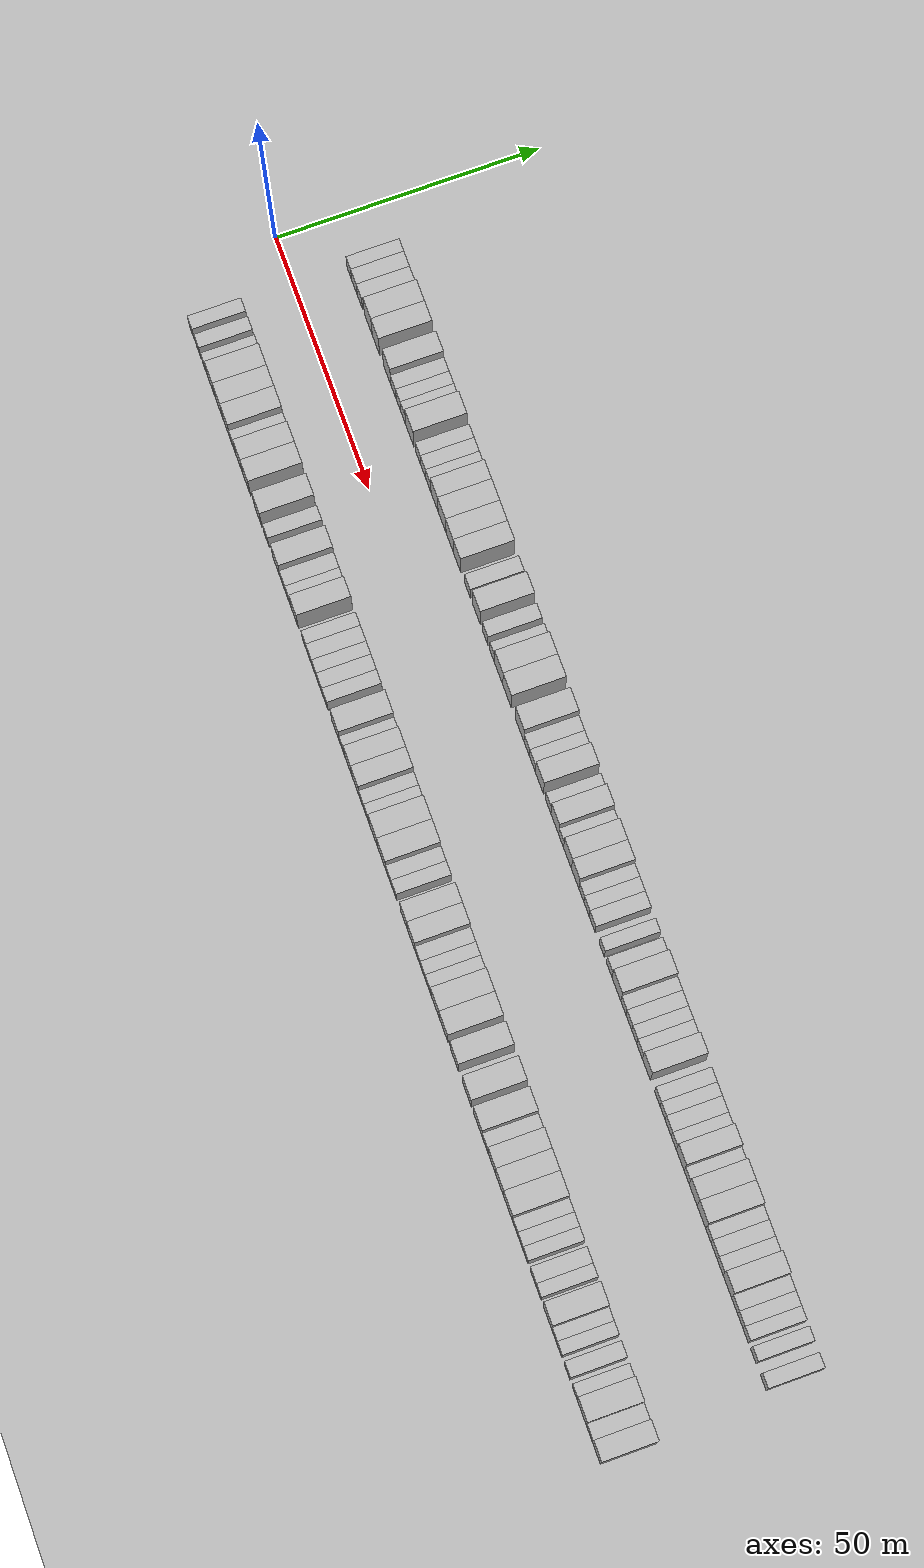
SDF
<?xml version="1.0" encoding="utf-8"?>

<sdf version="1.6">

   <world name="default">

      <gui fullscreen="0">

         <camera name="user_camera">

            <pose>-15 0 4.57585 0 0 0</pose>

            <view_controller>orbit</view_controller>

         </camera>

      </gui>

      <scene>

         <sky>

           <clouds>

             <speed>12</speed>

           </clouds>

         </sky>

         <ambient>0.4 0.4 0.4 1</ambient>

         <background>0.7 0.7 0.7 1</background>

         <shadows>1</shadows>

      </scene>

      <gravity>0 0 -9.8066</gravity>

      <magnetic_field>6e-06 2.3e-05 -4.2e-05</magnetic_field>

      <physics default="0" name="default_physics" type="ode">

         <ode>

            <solver>

               <type>quick</type>

               <iters>10</iters>

               <sor>1.0</sor>

               <use_dynamic_moi_rescaling>0</use_dynamic_moi_rescaling>

            </solver>

            <constraints>

               <cfm>0</cfm>

               <erp>0.2</erp>

               <contact_max_correcting_vel>100</contact_max_correcting_vel>

               <contact_surface_layer>0.001</contact_surface_layer>

            </constraints>

         </ode>

         <max_step_size>0.004</max_step_size>

         <real_time_factor>1</real_time_factor>

         <real_time_update_rate>250</real_time_update_rate>

      </physics>

      <light name="sun" type="directional">

         <cast_shadows>1</cast_shadows>

         <pose>0 0 10 0 0 0</pose>

         <diffuse>0.8 0.8 0.8 1</diffuse>

         <specular>0.2 0.2 0.2 1</specular>

         <attenuation>

            <range>1000</range>

            <constant>0.9</constant>

            <linear>0.01</linear>

            <quadratic>0.001</quadratic>

         </attenuation>

         <direction>-0.5 0.1 -0.9</direction>

      </light>

      <include>

         <name>ground_plane_1</name>

         <uri>model://HANNAS_ground_plane</uri>

         <pose>0 0 0  0 0 0</pose>

      </include>

      <include>

         <name>ground_plane_2</name>

         <uri>model://HANNAS_ground_plane</uri>

         <pose>100 0 0  0 0 0</pose>

      </include>

      <model name="building_1">

         <static>1</static>

         <pose frame="">11.2514 15.0000 0 0.000000 0.000000 1.570796</pose>

         <link name="link">

            <pose frame="">0 0 3.00 0 0 0</pose>

            <collision name="collision">

               <geometry>

                  <box>

                     <size>10.0000 2.5029 6.0000</size>

                  </box>

               </geometry>

               <max_contacts>10</max_contacts>

               <surface>

                  <contact>

                     <ode/>

                  </contact>

                  <bounce/>

                  <friction>

                     <torsional>

                        <ode/>

                     </torsional>

                     <ode/>

                  </friction>

               </surface>

            </collision>

            <visual name="visual">

               <cast_shadows>0</cast_shadows>

               <geometry>

                  <box>

                     <size>10.0000 2.5029 6.0000</size>

                  </box>

               </geometry>

               <material>

                  <script>

                     <uri>model://HANNAS_wall/materials/scripts</uri>

                     <uri>model://HANNAS_wall/materials/textures</uri>

                     <name>vrc/HANNAS_wall</name>

                  </script>

               </material>

            </visual>

            <self_collide>0</self_collide>

            <enable_wind>0</enable_wind>

            <kinematic>0</kinematic>

         </link>

      </model>

      <model name="building_2">

         <static>1</static>

         <pose frame="">14.0023 15.0000 0 0.000000 0.000000 1.570796</pose>

         <link name="link">

            <pose frame="">0 0 3.00 0 0 0</pose>

            <collision name="collision">

               <geometry>

                  <box>

                     <size>10.0000 2.9989 6.0000</size>

                  </box>

               </geometry>

               <max_contacts>10</max_contacts>

               <surface>

                  <contact>

                     <ode/>

                  </contact>

                  <bounce/>

                  <friction>

                     <torsional>

                        <ode/>

                     </torsional>

                     <ode/>

                  </friction>

               </surface>

            </collision>

            <visual name="visual">

               <cast_shadows>0</cast_shadows>

               <geometry>

                  <box>

                     <size>10.0000 2.9989 6.0000</size>

                  </box>

               </geometry>

               <material>

                  <script>

                     <uri>model://HANNAS_wall/materials/scripts</uri>

                     <uri>model://HANNAS_wall/materials/textures</uri>

                     <name>vrc/HANNAS_wall</name>

                  </script>

               </material>

            </visual>

            <self_collide>0</self_collide>

            <enable_wind>0</enable_wind>

            <kinematic>0</kinematic>

         </link>

      </model>

      <model name="building_3">

         <static>1</static>

         <pose frame="">16.9239 15.0000 0 0.000000 0.000000 1.570796</pose>

         <link name="link">

            <pose frame="">0 0 3.00 0 0 0</pose>

            <collision name="collision">

               <geometry>

                  <box>

                     <size>10.0000 2.8441 6.0000</size>

                  </box>

               </geometry>

               <max_contacts>10</max_contacts>

               <surface>

                  <contact>

                     <ode/>

                  </contact>

                  <bounce/>

                  <friction>

                     <torsional>

                        <ode/>

                     </torsional>

                     <ode/>

                  </friction>

               </surface>

            </collision>

            <visual name="visual">

               <cast_shadows>0</cast_shadows>

               <geometry>

                  <box>

                     <size>10.0000 2.8441 6.0000</size>

                  </box>

               </geometry>

               <material>

                  <script>

                     <uri>model://HANNAS_wall/materials/scripts</uri>

                     <uri>model://HANNAS_wall/materials/textures</uri>

                     <name>vrc/HANNAS_wall</name>

                  </script>

               </material>

            </visual>

            <self_collide>0</self_collide>

            <enable_wind>0</enable_wind>

            <kinematic>0</kinematic>

         </link>

      </model>

      <model name="building_4">

         <static>1</static>

         <pose frame="">21.4435 15.0000 0 0.000000 0.000000 1.570796</pose>

         <link name="link">

            <pose frame="">0 0 4.50 0 0 0</pose>

            <collision name="collision">

               <geometry>

                  <box>

                     <size>10.0000 4.1951 9.0000</size>

                  </box>

               </geometry>

               <max_contacts>10</max_contacts>

               <surface>

                  <contact>

                     <ode/>

                  </contact>

                  <bounce/>

                  <friction>

                     <torsional>

                        <ode/>

                     </torsional>

                     <ode/>

                  </friction>

               </surface>

            </collision>

            <visual name="visual">

               <cast_shadows>0</cast_shadows>

               <geometry>

                  <box>

                     <size>10.0000 4.1951 9.0000</size>

                  </box>

               </geometry>

               <material>

                  <script>

                     <uri>model://HANNAS_wall/materials/scripts</uri>

                     <uri>model://HANNAS_wall/materials/textures</uri>

                     <name>vrc/HANNAS_wall</name>

                  </script>

               </material>

            </visual>

            <self_collide>0</self_collide>

            <enable_wind>0</enable_wind>

            <kinematic>0</kinematic>

         </link>

      </model>

      <model name="building_5">

         <static>1</static>

         <pose frame="">25.5285 15.0000 0 0.000000 0.000000 1.570796</pose>

         <link name="link">

            <pose frame="">0 0 4.50 0 0 0</pose>

            <collision name="collision">

               <geometry>

                  <box>

                     <size>10.0000 3.9750 9.0000</size>

                  </box>

               </geometry>

               <max_contacts>10</max_contacts>

               <surface>

                  <contact>

                     <ode/>

                  </contact>

                  <bounce/>

                  <friction>

                     <torsional>

                        <ode/>

                     </torsional>

                     <ode/>

                  </friction>

               </surface>

            </collision>

            <visual name="visual">

               <cast_shadows>0</cast_shadows>

               <geometry>

                  <box>

                     <size>10.0000 3.9750 9.0000</size>

                  </box>

               </geometry>

               <material>

                  <script>

                     <uri>model://HANNAS_wall/materials/scripts</uri>

                     <uri>model://HANNAS_wall/materials/textures</uri>

                     <name>vrc/HANNAS_wall</name>

                  </script>

               </material>

            </visual>

            <self_collide>0</self_collide>

            <enable_wind>0</enable_wind>

            <kinematic>0</kinematic>

         </link>

      </model>

      <model name="building_6">

         <static>1</static>

         <pose frame="">31.5260 15.0000 0 0.000000 0.000000 1.570796</pose>

         <link name="link">

            <pose frame="">0 0 4.50 0 0 0</pose>

            <collision name="collision">

               <geometry>

                  <box>

                     <size>10.0000 4.0201 9.0000</size>

                  </box>

               </geometry>

               <max_contacts>10</max_contacts>

               <surface>

                  <contact>

                     <ode/>

                  </contact>

                  <bounce/>

                  <friction>

                     <torsional>

                        <ode/>

                     </torsional>

                     <ode/>

                  </friction>

               </surface>

            </collision>

            <visual name="visual">

               <cast_shadows>0</cast_shadows>

               <geometry>

                  <box>

                     <size>10.0000 4.0201 9.0000</size>

                  </box>

               </geometry>

               <material>

                  <script>

                     <uri>model://HANNAS_wall/materials/scripts</uri>

                     <uri>model://HANNAS_wall/materials/textures</uri>

                     <name>vrc/HANNAS_wall</name>

                  </script>

               </material>

            </visual>

            <self_collide>0</self_collide>

            <enable_wind>0</enable_wind>

            <kinematic>0</kinematic>

         </link>

      </model>

      <model name="building_7">

         <static>1</static>

         <pose frame="">34.9230 15.0000 0 0.000000 0.000000 1.570796</pose>

         <link name="link">

            <pose frame="">0 0 3.00 0 0 0</pose>

            <collision name="collision">

               <geometry>

                  <box>

                     <size>10.0000 2.7737 6.0000</size>

                  </box>

               </geometry>

               <max_contacts>10</max_contacts>

               <surface>

                  <contact>

                     <ode/>

                  </contact>

                  <bounce/>

                  <friction>

                     <torsional>

                        <ode/>

                     </torsional>

                     <ode/>

                  </friction>

               </surface>

            </collision>

            <visual name="visual">

               <cast_shadows>0</cast_shadows>

               <geometry>

                  <box>

                     <size>10.0000 2.7737 6.0000</size>

                  </box>

               </geometry>

               <material>

                  <script>

                     <uri>model://HANNAS_wall/materials/scripts</uri>

                     <uri>model://HANNAS_wall/materials/textures</uri>

                     <name>vrc/HANNAS_wall</name>

                  </script>

               </material>

            </visual>

            <self_collide>0</self_collide>

            <enable_wind>0</enable_wind>

            <kinematic>0</kinematic>

         </link>

      </model>

      <model name="building_8">

         <static>1</static>

         <pose frame="">37.5219 15.0000 0 0.000000 0.000000 1.570796</pose>

         <link name="link">

            <pose frame="">0 0 3.00 0 0 0</pose>

            <collision name="collision">

               <geometry>

                  <box>

                     <size>10.0000 2.4242 6.0000</size>

                  </box>

               </geometry>

               <max_contacts>10</max_contacts>

               <surface>

                  <contact>

                     <ode/>

                  </contact>

                  <bounce/>

                  <friction>

                     <torsional>

                        <ode/>

                     </torsional>

                     <ode/>

                  </friction>

               </surface>

            </collision>

            <visual name="visual">

               <cast_shadows>0</cast_shadows>

               <geometry>

                  <box>

                     <size>10.0000 2.4242 6.0000</size>

                  </box>

               </geometry>

               <material>

                  <script>

                     <uri>model://HANNAS_wall/materials/scripts</uri>

                     <uri>model://HANNAS_wall/materials/textures</uri>

                     <name>vrc/HANNAS_wall</name>

                  </script>

               </material>

            </visual>

            <self_collide>0</self_collide>

            <enable_wind>0</enable_wind>

            <kinematic>0</kinematic>

         </link>

      </model>

      <model name="building_9">

         <static>1</static>

         <pose frame="">40.0258 15.0000 0 0.000000 0.000000 1.570796</pose>

         <link name="link">

            <pose frame="">0 0 3.00 0 0 0</pose>

            <collision name="collision">

               <geometry>

                  <box>

                     <size>10.0000 2.5834 6.0000</size>

                  </box>

               </geometry>

               <max_contacts>10</max_contacts>

               <surface>

                  <contact>

                     <ode/>

                  </contact>

                  <bounce/>

                  <friction>

                     <torsional>

                        <ode/>

                     </torsional>

                     <ode/>

                  </friction>

               </surface>

            </collision>

            <visual name="visual">

               <cast_shadows>0</cast_shadows>

               <geometry>

                  <box>

                     <size>10.0000 2.5834 6.0000</size>

                  </box>

               </geometry>

               <material>

                  <script>

                     <uri>model://HANNAS_wall/materials/scripts</uri>

                     <uri>model://HANNAS_wall/materials/textures</uri>

                     <name>vrc/HANNAS_wall</name>

                  </script>

               </material>

            </visual>

            <self_collide>0</self_collide>

            <enable_wind>0</enable_wind>

            <kinematic>0</kinematic>

         </link>

      </model>

      <model name="building_10">

         <static>1</static>

         <pose frame="">43.4983 15.0000 0 0.000000 0.000000 1.570796</pose>

         <link name="link">

            <pose frame="">0 0 4.50 0 0 0</pose>

            <collision name="collision">

               <geometry>

                  <box>

                     <size>10.0000 4.3616 9.0000</size>

                  </box>

               </geometry>

               <max_contacts>10</max_contacts>

               <surface>

                  <contact>

                     <ode/>

                  </contact>

                  <bounce/>

                  <friction>

                     <torsional>

                        <ode/>

                     </torsional>

                     <ode/>

                  </friction>

               </surface>

            </collision>

            <visual name="visual">

               <cast_shadows>0</cast_shadows>

               <geometry>

                  <box>

                     <size>10.0000 4.3616 9.0000</size>

                  </box>

               </geometry>

               <material>

                  <script>

                     <uri>model://HANNAS_wall/materials/scripts</uri>

                     <uri>model://HANNAS_wall/materials/textures</uri>

                     <name>vrc/HANNAS_wall</name>

                  </script>

               </material>

            </visual>

            <self_collide>0</self_collide>

            <enable_wind>0</enable_wind>

            <kinematic>0</kinematic>

         </link>

      </model>

      <model name="building_11">

         <static>1</static>

         <pose frame="">47.9770 15.0000 0 0.000000 0.000000 1.570796</pose>

         <link name="link">

            <pose frame="">0 0 3.00 0 0 0</pose>

            <collision name="collision">

               <geometry>

                  <box>

                     <size>10.0000 2.5957 6.0000</size>

                  </box>

               </geometry>

               <max_contacts>10</max_contacts>

               <surface>

                  <contact>

                     <ode/>

                  </contact>

                  <bounce/>

                  <friction>

                     <torsional>

                        <ode/>

                     </torsional>

                     <ode/>

                  </friction>

               </surface>

            </collision>

            <visual name="visual">

               <cast_shadows>0</cast_shadows>

               <geometry>

                  <box>

                     <size>10.0000 2.5957 6.0000</size>

                  </box>

               </geometry>

               <material>

                  <script>

                     <uri>model://HANNAS_wall/materials/scripts</uri>

                     <uri>model://HANNAS_wall/materials/textures</uri>

                     <name>vrc/HANNAS_wall</name>

                  </script>

               </material>

            </visual>

            <self_collide>0</self_collide>

            <enable_wind>0</enable_wind>

            <kinematic>0</kinematic>

         </link>

      </model>

      <model name="building_12">

         <static>1</static>

         <pose frame="">50.6294 15.0000 0 0.000000 0.000000 1.570796</pose>

         <link name="link">

            <pose frame="">0 0 3.00 0 0 0</pose>

            <collision name="collision">

               <geometry>

                  <box>

                     <size>10.0000 2.7092 6.0000</size>

                  </box>

               </geometry>

               <max_contacts>10</max_contacts>

               <surface>

                  <contact>

                     <ode/>

                  </contact>

                  <bounce/>

                  <friction>

                     <torsional>

                        <ode/>

                     </torsional>

                     <ode/>

                  </friction>

               </surface>

            </collision>

            <visual name="visual">

               <cast_shadows>0</cast_shadows>

               <geometry>

                  <box>

                     <size>10.0000 2.7092 6.0000</size>

                  </box>

               </geometry>

               <material>

                  <script>

                     <uri>model://HANNAS_wall/materials/scripts</uri>

                     <uri>model://HANNAS_wall/materials/textures</uri>

                     <name>vrc/HANNAS_wall</name>

                  </script>

               </material>

            </visual>

            <self_collide>0</self_collide>

            <enable_wind>0</enable_wind>

            <kinematic>0</kinematic>

         </link>

      </model>

      <model name="building_13">

         <static>1</static>

         <pose frame="">53.3160 15.0000 0 0.000000 0.000000 1.570796</pose>

         <link name="link">

            <pose frame="">0 0 3.00 0 0 0</pose>

            <collision name="collision">

               <geometry>

                  <box>

                     <size>10.0000 2.6641 6.0000</size>

                  </box>

               </geometry>

               <max_contacts>10</max_contacts>

               <surface>

                  <contact>

                     <ode/>

                  </contact>

                  <bounce/>

                  <friction>

                     <torsional>

                        <ode/>

                     </torsional>

                     <ode/>

                  </friction>

               </surface>

            </collision>

            <visual name="visual">

               <cast_shadows>0</cast_shadows>

               <geometry>

                  <box>

                     <size>10.0000 2.6641 6.0000</size>

                  </box>

               </geometry>

               <material>

                  <script>

                     <uri>model://HANNAS_wall/materials/scripts</uri>

                     <uri>model://HANNAS_wall/materials/textures</uri>

                     <name>vrc/HANNAS_wall</name>

                  </script>

               </material>

            </visual>

            <self_collide>0</self_collide>

            <enable_wind>0</enable_wind>

            <kinematic>0</kinematic>

         </link>

      </model>

      <model name="building_14">

         <static>1</static>

         <pose frame="">56.5004 15.0000 0 0.000000 0.000000 1.570796</pose>

         <link name="link">

            <pose frame="">0 0 4.50 0 0 0</pose>

            <collision name="collision">

               <geometry>

                  <box>

                     <size>10.0000 3.7046 9.0000</size>

                  </box>

               </geometry>

               <max_contacts>10</max_contacts>

               <surface>

                  <contact>

                     <ode/>

                  </contact>

                  <bounce/>

                  <friction>

                     <torsional>

                        <ode/>

                     </torsional>

                     <ode/>

                  </friction>

               </surface>

            </collision>

            <visual name="visual">

               <cast_shadows>0</cast_shadows>

               <geometry>

                  <box>

                     <size>10.0000 3.7046 9.0000</size>

                  </box>

               </geometry>

               <material>

                  <script>

                     <uri>model://HANNAS_wall/materials/scripts</uri>

                     <uri>model://HANNAS_wall/materials/textures</uri>

                     <name>vrc/HANNAS_wall</name>

                  </script>

               </material>

            </visual>

            <self_collide>0</self_collide>

            <enable_wind>0</enable_wind>

            <kinematic>0</kinematic>

         </link>

      </model>

      <model name="building_15">

         <static>1</static>

         <pose frame="">60.4283 15.0000 0 0.000000 0.000000 1.570796</pose>

         <link name="link">

            <pose frame="">0 0 4.50 0 0 0</pose>

            <collision name="collision">

               <geometry>

                  <box>

                     <size>10.0000 4.1512 9.0000</size>

                  </box>

               </geometry>

               <max_contacts>10</max_contacts>

               <surface>

                  <contact>

                     <ode/>

                  </contact>

                  <bounce/>

                  <friction>

                     <torsional>

                        <ode/>

                     </torsional>

                     <ode/>

                  </friction>

               </surface>

            </collision>

            <visual name="visual">

               <cast_shadows>0</cast_shadows>

               <geometry>

                  <box>

                     <size>10.0000 4.1512 9.0000</size>

                  </box>

               </geometry>

               <material>

                  <script>

                     <uri>model://HANNAS_wall/materials/scripts</uri>

                     <uri>model://HANNAS_wall/materials/textures</uri>

                     <name>vrc/HANNAS_wall</name>

                  </script>

               </material>

            </visual>

            <self_collide>0</self_collide>

            <enable_wind>0</enable_wind>

            <kinematic>0</kinematic>

         </link>

      </model>

      <model name="building_16">

         <static>1</static>

         <pose frame="">64.4689 15.0000 0 0.000000 0.000000 1.570796</pose>

         <link name="link">

            <pose frame="">0 0 4.50 0 0 0</pose>

            <collision name="collision">

               <geometry>

                  <box>

                     <size>10.0000 3.9300 9.0000</size>

                  </box>

               </geometry>

               <max_contacts>10</max_contacts>

               <surface>

                  <contact>

                     <ode/>

                  </contact>

                  <bounce/>

                  <friction>

                     <torsional>

                        <ode/>

                     </torsional>

                     <ode/>

                  </friction>

               </surface>

            </collision>

            <visual name="visual">

               <cast_shadows>0</cast_shadows>

               <geometry>

                  <box>

                     <size>10.0000 3.9300 9.0000</size>

                  </box>

               </geometry>

               <material>

                  <script>

                     <uri>model://HANNAS_wall/materials/scripts</uri>

                     <uri>model://HANNAS_wall/materials/textures</uri>

                     <name>vrc/HANNAS_wall</name>

                  </script>

               </material>

            </visual>

            <self_collide>0</self_collide>

            <enable_wind>0</enable_wind>

            <kinematic>0</kinematic>

         </link>

      </model>

      <model name="building_17">

         <static>1</static>

         <pose frame="">68.3168 15.0000 0 0.000000 0.000000 1.570796</pose>

         <link name="link">

            <pose frame="">0 0 4.50 0 0 0</pose>

            <collision name="collision">

               <geometry>

                  <box>

                     <size>10.0000 3.7660 9.0000</size>

                  </box>

               </geometry>

               <max_contacts>10</max_contacts>

               <surface>

                  <contact>

                     <ode/>

                  </contact>

                  <bounce/>

                  <friction>

                     <torsional>

                        <ode/>

                     </torsional>

                     <ode/>

                  </friction>

               </surface>

            </collision>

            <visual name="visual">

               <cast_shadows>0</cast_shadows>

               <geometry>

                  <box>

                     <size>10.0000 3.7660 9.0000</size>

                  </box>

               </geometry>

               <material>

                  <script>

                     <uri>model://HANNAS_wall/materials/scripts</uri>

                     <uri>model://HANNAS_wall/materials/textures</uri>

                     <name>vrc/HANNAS_wall</name>

                  </script>

               </material>

            </visual>

            <self_collide>0</self_collide>

            <enable_wind>0</enable_wind>

            <kinematic>0</kinematic>

         </link>

      </model>

      <model name="building_18">

         <static>1</static>

         <pose frame="">73.6593 15.0000 0 0.000000 0.000000 1.570796</pose>

         <link name="link">

            <pose frame="">0 0 3.00 0 0 0</pose>

            <collision name="collision">

               <geometry>

                  <box>

                     <size>10.0000 2.9189 6.0000</size>

                  </box>

               </geometry>

               <max_contacts>10</max_contacts>

               <surface>

                  <contact>

                     <ode/>

                  </contact>

                  <bounce/>

                  <friction>

                     <torsional>

                        <ode/>

                     </torsional>

                     <ode/>

                  </friction>

               </surface>

            </collision>

            <visual name="visual">

               <cast_shadows>0</cast_shadows>

               <geometry>

                  <box>

                     <size>10.0000 2.9189 6.0000</size>

                  </box>

               </geometry>

               <material>

                  <script>

                     <uri>model://HANNAS_wall/materials/scripts</uri>

                     <uri>model://HANNAS_wall/materials/textures</uri>

                     <name>vrc/HANNAS_wall</name>

                  </script>

               </material>

            </visual>

            <self_collide>0</self_collide>

            <enable_wind>0</enable_wind>

            <kinematic>0</kinematic>

         </link>

      </model>

      <model name="building_19">

         <static>1</static>

         <pose frame="">78.1737 15.0000 0 0.000000 0.000000 1.570796</pose>

         <link name="link">

            <pose frame="">0 0 4.50 0 0 0</pose>

            <collision name="collision">

               <geometry>

                  <box>

                     <size>10.0000 4.1099 9.0000</size>

                  </box>

               </geometry>

               <max_contacts>10</max_contacts>

               <surface>

                  <contact>

                     <ode/>

                  </contact>

                  <bounce/>

                  <friction>

                     <torsional>

                        <ode/>

                     </torsional>

                     <ode/>

                  </friction>

               </surface>

            </collision>

            <visual name="visual">

               <cast_shadows>0</cast_shadows>

               <geometry>

                  <box>

                     <size>10.0000 4.1099 9.0000</size>

                  </box>

               </geometry>

               <material>

                  <script>

                     <uri>model://HANNAS_wall/materials/scripts</uri>

                     <uri>model://HANNAS_wall/materials/textures</uri>

                     <name>vrc/HANNAS_wall</name>

                  </script>

               </material>

            </visual>

            <self_collide>0</self_collide>

            <enable_wind>0</enable_wind>

            <kinematic>0</kinematic>

         </link>

      </model>

      <model name="building_20">

         <static>1</static>

         <pose frame="">82.6827 15.0000 0 0.000000 0.000000 1.570796</pose>

         <link name="link">

            <pose frame="">0 0 3.00 0 0 0</pose>

            <collision name="collision">

               <geometry>

                  <box>

                     <size>10.0000 2.9082 6.0000</size>

                  </box>

               </geometry>

               <max_contacts>10</max_contacts>

               <surface>

                  <contact>

                     <ode/>

                  </contact>

                  <bounce/>

                  <friction>

                     <torsional>

                        <ode/>

                     </torsional>

                     <ode/>

                  </friction>

               </surface>

            </collision>

            <visual name="visual">

               <cast_shadows>0</cast_shadows>

               <geometry>

                  <box>

                     <size>10.0000 2.9082 6.0000</size>

                  </box>

               </geometry>

               <material>

                  <script>

                     <uri>model://HANNAS_wall/materials/scripts</uri>

                     <uri>model://HANNAS_wall/materials/textures</uri>

                     <name>vrc/HANNAS_wall</name>

                  </script>

               </material>

            </visual>

            <self_collide>0</self_collide>

            <enable_wind>0</enable_wind>

            <kinematic>0</kinematic>

         </link>

      </model>

      <model name="building_21">

         <static>1</static>

         <pose frame="">86.3541 15.0000 0 0.000000 0.000000 1.570796</pose>

         <link name="link">

            <pose frame="">0 0 3.00 0 0 0</pose>

            <collision name="collision">

               <geometry>

                  <box>

                     <size>10.0000 2.4345 6.0000</size>

                  </box>

               </geometry>

               <max_contacts>10</max_contacts>

               <surface>

                  <contact>

                     <ode/>

                  </contact>

                  <bounce/>

                  <friction>

                     <torsional>

                        <ode/>

                     </torsional>

                     <ode/>

                  </friction>

               </surface>

            </collision>

            <visual name="visual">

               <cast_shadows>0</cast_shadows>

               <geometry>

                  <box>

                     <size>10.0000 2.4345 6.0000</size>

                  </box>

               </geometry>

               <material>

                  <script>

                     <uri>model://HANNAS_wall/materials/scripts</uri>

                     <uri>model://HANNAS_wall/materials/textures</uri>

                     <name>vrc/HANNAS_wall</name>

                  </script>

               </material>

            </visual>

            <self_collide>0</self_collide>

            <enable_wind>0</enable_wind>

            <kinematic>0</kinematic>

         </link>

      </model>

      <model name="building_22">

         <static>1</static>

         <pose frame="">89.6806 15.0000 0 0.000000 0.000000 1.570796</pose>

         <link name="link">

            <pose frame="">0 0 4.50 0 0 0</pose>

            <collision name="collision">

               <geometry>

                  <box>

                     <size>10.0000 4.2186 9.0000</size>

                  </box>

               </geometry>

               <max_contacts>10</max_contacts>

               <surface>

                  <contact>

                     <ode/>

                  </contact>

                  <bounce/>

                  <friction>

                     <torsional>

                        <ode/>

                     </torsional>

                     <ode/>

                  </friction>

               </surface>

            </collision>

            <visual name="visual">

               <cast_shadows>0</cast_shadows>

               <geometry>

                  <box>

                     <size>10.0000 4.2186 9.0000</size>

                  </box>

               </geometry>

               <material>

                  <script>

                     <uri>model://HANNAS_wall/materials/scripts</uri>

                     <uri>model://HANNAS_wall/materials/textures</uri>

                     <name>vrc/HANNAS_wall</name>

                  </script>

               </material>

            </visual>

            <self_collide>0</self_collide>

            <enable_wind>0</enable_wind>

            <kinematic>0</kinematic>

         </link>

      </model>

      <model name="building_23">

         <static>1</static>

         <pose frame="">93.9344 15.0000 0 0.000000 0.000000 1.570796</pose>

         <link name="link">

            <pose frame="">0 0 4.50 0 0 0</pose>

            <collision name="collision">

               <geometry>

                  <box>

                     <size>10.0000 4.2889 9.0000</size>

                  </box>

               </geometry>

               <max_contacts>10</max_contacts>

               <surface>

                  <contact>

                     <ode/>

                  </contact>

                  <bounce/>

                  <friction>

                     <torsional>

                        <ode/>

                     </torsional>

                     <ode/>

                  </friction>

               </surface>

            </collision>

            <visual name="visual">

               <cast_shadows>0</cast_shadows>

               <geometry>

                  <box>

                     <size>10.0000 4.2889 9.0000</size>

                  </box>

               </geometry>

               <material>

                  <script>

                     <uri>model://HANNAS_wall/materials/scripts</uri>

                     <uri>model://HANNAS_wall/materials/textures</uri>

                     <name>vrc/HANNAS_wall</name>

                  </script>

               </material>

            </visual>

            <self_collide>0</self_collide>

            <enable_wind>0</enable_wind>

            <kinematic>0</kinematic>

         </link>

      </model>

      <model name="building_24">

         <static>1</static>

         <pose frame="">100.2766 15.0000 0 0.000000 0.000000 1.570796</pose>

         <link name="link">

            <pose frame="">0 0 4.50 0 0 0</pose>

            <collision name="collision">

               <geometry>

                  <box>

                     <size>10.0000 4.3954 9.0000</size>

                  </box>

               </geometry>

               <max_contacts>10</max_contacts>

               <surface>

                  <contact>

                     <ode/>

                  </contact>

                  <bounce/>

                  <friction>

                     <torsional>

                        <ode/>

                     </torsional>

                     <ode/>

                  </friction>

               </surface>

            </collision>

            <visual name="visual">

               <cast_shadows>0</cast_shadows>

               <geometry>

                  <box>

                     <size>10.0000 4.3954 9.0000</size>

                  </box>

               </geometry>

               <material>

                  <script>

                     <uri>model://HANNAS_wall/materials/scripts</uri>

                     <uri>model://HANNAS_wall/materials/textures</uri>

                     <name>vrc/HANNAS_wall</name>

                  </script>

               </material>

            </visual>

            <self_collide>0</self_collide>

            <enable_wind>0</enable_wind>

            <kinematic>0</kinematic>

         </link>

      </model>

      <model name="building_25">

         <static>1</static>

         <pose frame="">103.9257 15.0000 0 0.000000 0.000000 1.570796</pose>

         <link name="link">

            <pose frame="">0 0 3.00 0 0 0</pose>

            <collision name="collision">

               <geometry>

                  <box>

                     <size>10.0000 2.9029 6.0000</size>

                  </box>

               </geometry>

               <max_contacts>10</max_contacts>

               <surface>

                  <contact>

                     <ode/>

                  </contact>

                  <bounce/>

                  <friction>

                     <torsional>

                        <ode/>

                     </torsional>

                     <ode/>

                  </friction>

               </surface>

            </collision>

            <visual name="visual">

               <cast_shadows>0</cast_shadows>

               <geometry>

                  <box>

                     <size>10.0000 2.9029 6.0000</size>

                  </box>

               </geometry>

               <material>

                  <script>

                     <uri>model://HANNAS_wall/materials/scripts</uri>

                     <uri>model://HANNAS_wall/materials/textures</uri>

                     <name>vrc/HANNAS_wall</name>

                  </script>

               </material>

            </visual>

            <self_collide>0</self_collide>

            <enable_wind>0</enable_wind>

            <kinematic>0</kinematic>

         </link>

      </model>

      <model name="building_26">

         <static>1</static>

         <pose frame="">106.8754 15.0000 0 0.000000 0.000000 1.570796</pose>

         <link name="link">

            <pose frame="">0 0 3.00 0 0 0</pose>

            <collision name="collision">

               <geometry>

                  <box>

                     <size>10.0000 2.9966 6.0000</size>

                  </box>

               </geometry>

               <max_contacts>10</max_contacts>

               <surface>

                  <contact>

                     <ode/>

                  </contact>

                  <bounce/>

                  <friction>

                     <torsional>

                        <ode/>

                     </torsional>

                     <ode/>

                  </friction>

               </surface>

            </collision>

            <visual name="visual">

               <cast_shadows>0</cast_shadows>

               <geometry>

                  <box>

                     <size>10.0000 2.9966 6.0000</size>

                  </box>

               </geometry>

               <material>

                  <script>

                     <uri>model://HANNAS_wall/materials/scripts</uri>

                     <uri>model://HANNAS_wall/materials/textures</uri>

                     <name>vrc/HANNAS_wall</name>

                  </script>

               </material>

            </visual>

            <self_collide>0</self_collide>

            <enable_wind>0</enable_wind>

            <kinematic>0</kinematic>

         </link>

      </model>

      <model name="building_27">

         <static>1</static>

         <pose frame="">110.3782 15.0000 0 0.000000 0.000000 1.570796</pose>

         <link name="link">

            <pose frame="">0 0 4.50 0 0 0</pose>

            <collision name="collision">

               <geometry>

                  <box>

                     <size>10.0000 4.0090 9.0000</size>

                  </box>

               </geometry>

               <max_contacts>10</max_contacts>

               <surface>

                  <contact>

                     <ode/>

                  </contact>

                  <bounce/>

                  <friction>

                     <torsional>

                        <ode/>

                     </torsional>

                     <ode/>

                  </friction>

               </surface>

            </collision>

            <visual name="visual">

               <cast_shadows>0</cast_shadows>

               <geometry>

                  <box>

                     <size>10.0000 4.0090 9.0000</size>

                  </box>

               </geometry>

               <material>

                  <script>

                     <uri>model://HANNAS_wall/materials/scripts</uri>

                     <uri>model://HANNAS_wall/materials/textures</uri>

                     <name>vrc/HANNAS_wall</name>

                  </script>

               </material>

            </visual>

            <self_collide>0</self_collide>

            <enable_wind>0</enable_wind>

            <kinematic>0</kinematic>

         </link>

      </model>

      <model name="building_28">

         <static>1</static>

         <pose frame="">114.7304 15.0000 0 0.000000 0.000000 1.570796</pose>

         <link name="link">

            <pose frame="">0 0 3.00 0 0 0</pose>

            <collision name="collision">

               <geometry>

                  <box>

                     <size>10.0000 2.6954 6.0000</size>

                  </box>

               </geometry>

               <max_contacts>10</max_contacts>

               <surface>

                  <contact>

                     <ode/>

                  </contact>

                  <bounce/>

                  <friction>

                     <torsional>

                        <ode/>

                     </torsional>

                     <ode/>

                  </friction>

               </surface>

            </collision>

            <visual name="visual">

               <cast_shadows>0</cast_shadows>

               <geometry>

                  <box>

                     <size>10.0000 2.6954 6.0000</size>

                  </box>

               </geometry>

               <material>

                  <script>

                     <uri>model://HANNAS_wall/materials/scripts</uri>

                     <uri>model://HANNAS_wall/materials/textures</uri>

                     <name>vrc/HANNAS_wall</name>

                  </script>

               </material>

            </visual>

            <self_collide>0</self_collide>

            <enable_wind>0</enable_wind>

            <kinematic>0</kinematic>

         </link>

      </model>

      <model name="building_29">

         <static>1</static>

         <pose frame="">118.0491 15.0000 0 0.000000 0.000000 1.570796</pose>

         <link name="link">

            <pose frame="">0 0 4.50 0 0 0</pose>

            <collision name="collision">

               <geometry>

                  <box>

                     <size>10.0000 3.9418 9.0000</size>

                  </box>

               </geometry>

               <max_contacts>10</max_contacts>

               <surface>

                  <contact>

                     <ode/>

                  </contact>

                  <bounce/>

                  <friction>

                     <torsional>

                        <ode/>

                     </torsional>

                     <ode/>

                  </friction>

               </surface>

            </collision>

            <visual name="visual">

               <cast_shadows>0</cast_shadows>

               <geometry>

                  <box>

                     <size>10.0000 3.9418 9.0000</size>

                  </box>

               </geometry>

               <material>

                  <script>

                     <uri>model://HANNAS_wall/materials/scripts</uri>

                     <uri>model://HANNAS_wall/materials/textures</uri>

                     <name>vrc/HANNAS_wall</name>

                  </script>

               </material>

            </visual>

            <self_collide>0</self_collide>

            <enable_wind>0</enable_wind>

            <kinematic>0</kinematic>

         </link>

      </model>

      <model name="building_30">

         <static>1</static>

         <pose frame="">121.2317 15.0000 0 0.000000 0.000000 1.570796</pose>

         <link name="link">

            <pose frame="">0 0 3.00 0 0 0</pose>

            <collision name="collision">

               <geometry>

                  <box>

                     <size>10.0000 2.4235 6.0000</size>

                  </box>

               </geometry>

               <max_contacts>10</max_contacts>

               <surface>

                  <contact>

                     <ode/>

                  </contact>

                  <bounce/>

                  <friction>

                     <torsional>

                        <ode/>

                     </torsional>

                     <ode/>

                  </friction>

               </surface>

            </collision>

            <visual name="visual">

               <cast_shadows>0</cast_shadows>

               <geometry>

                  <box>

                     <size>10.0000 2.4235 6.0000</size>

                  </box>

               </geometry>

               <material>

                  <script>

                     <uri>model://HANNAS_wall/materials/scripts</uri>

                     <uri>model://HANNAS_wall/materials/textures</uri>

                     <name>vrc/HANNAS_wall</name>

                  </script>

               </material>

            </visual>

            <self_collide>0</self_collide>

            <enable_wind>0</enable_wind>

            <kinematic>0</kinematic>

         </link>

      </model>

      <model name="building_31">

         <static>1</static>

         <pose frame="">124.4070 15.0000 0 0.000000 0.000000 1.570796</pose>

         <link name="link">

            <pose frame="">0 0 4.50 0 0 0</pose>

            <collision name="collision">

               <geometry>

                  <box>

                     <size>10.0000 3.9272 9.0000</size>

                  </box>

               </geometry>

               <max_contacts>10</max_contacts>

               <surface>

                  <contact>

                     <ode/>

                  </contact>

                  <bounce/>

                  <friction>

                     <torsional>

                        <ode/>

                     </torsional>

                     <ode/>

                  </friction>

               </surface>

            </collision>

            <visual name="visual">

               <cast_shadows>0</cast_shadows>

               <geometry>

                  <box>

                     <size>10.0000 3.9272 9.0000</size>

                  </box>

               </geometry>

               <material>

                  <script>

                     <uri>model://HANNAS_wall/materials/scripts</uri>

                     <uri>model://HANNAS_wall/materials/textures</uri>

                     <name>vrc/HANNAS_wall</name>

                  </script>

               </material>

            </visual>

            <self_collide>0</self_collide>

            <enable_wind>0</enable_wind>

            <kinematic>0</kinematic>

         </link>

      </model>

      <model name="building_32">

         <static>1</static>

         <pose frame="">128.2069 15.0000 0 0.000000 0.000000 1.570796</pose>

         <link name="link">

            <pose frame="">0 0 4.50 0 0 0</pose>

            <collision name="collision">

               <geometry>

                  <box>

                     <size>10.0000 3.6725 9.0000</size>

                  </box>

               </geometry>

               <max_contacts>10</max_contacts>

               <surface>

                  <contact>

                     <ode/>

                  </contact>

                  <bounce/>

                  <friction>

                     <torsional>

                        <ode/>

                     </torsional>

                     <ode/>

                  </friction>

               </surface>

            </collision>

            <visual name="visual">

               <cast_shadows>0</cast_shadows>

               <geometry>

                  <box>

                     <size>10.0000 3.6725 9.0000</size>

                  </box>

               </geometry>

               <material>

                  <script>

                     <uri>model://HANNAS_wall/materials/scripts</uri>

                     <uri>model://HANNAS_wall/materials/textures</uri>

                     <name>vrc/HANNAS_wall</name>

                  </script>

               </material>

            </visual>

            <self_collide>0</self_collide>

            <enable_wind>0</enable_wind>

            <kinematic>0</kinematic>

         </link>

      </model>

      <model name="building_33">

         <static>1</static>

         <pose frame="">131.2854 15.0000 0 0.000000 0.000000 1.570796</pose>

         <link name="link">

            <pose frame="">0 0 3.00 0 0 0</pose>

            <collision name="collision">

               <geometry>

                  <box>

                     <size>10.0000 2.4846 6.0000</size>

                  </box>

               </geometry>

               <max_contacts>10</max_contacts>

               <surface>

                  <contact>

                     <ode/>

                  </contact>

                  <bounce/>

                  <friction>

                     <torsional>

                        <ode/>

                     </torsional>

                     <ode/>

                  </friction>

               </surface>

            </collision>

            <visual name="visual">

               <cast_shadows>0</cast_shadows>

               <geometry>

                  <box>

                     <size>10.0000 2.4846 6.0000</size>

                  </box>

               </geometry>

               <material>

                  <script>

                     <uri>model://HANNAS_wall/materials/scripts</uri>

                     <uri>model://HANNAS_wall/materials/textures</uri>

                     <name>vrc/HANNAS_wall</name>

                  </script>

               </material>

            </visual>

            <self_collide>0</self_collide>

            <enable_wind>0</enable_wind>

            <kinematic>0</kinematic>

         </link>

      </model>

      <model name="building_34">

         <static>1</static>

         <pose frame="">133.8589 15.0000 0 0.000000 0.000000 1.570796</pose>

         <link name="link">

            <pose frame="">0 0 3.00 0 0 0</pose>

            <collision name="collision">

               <geometry>

                  <box>

                     <size>10.0000 2.6624 6.0000</size>

                  </box>

               </geometry>

               <max_contacts>10</max_contacts>

               <surface>

                  <contact>

                     <ode/>

                  </contact>

                  <bounce/>

                  <friction>

                     <torsional>

                        <ode/>

                     </torsional>

                     <ode/>

                  </friction>

               </surface>

            </collision>

            <visual name="visual">

               <cast_shadows>0</cast_shadows>

               <geometry>

                  <box>

                     <size>10.0000 2.6624 6.0000</size>

                  </box>

               </geometry>

               <material>

                  <script>

                     <uri>model://HANNAS_wall/materials/scripts</uri>

                     <uri>model://HANNAS_wall/materials/textures</uri>

                     <name>vrc/HANNAS_wall</name>

                  </script>

               </material>

            </visual>

            <self_collide>0</self_collide>

            <enable_wind>0</enable_wind>

            <kinematic>0</kinematic>

         </link>

      </model>

      <model name="building_35">

         <static>1</static>

         <pose frame="">136.6706 15.0000 0 0.000000 0.000000 1.570796</pose>

         <link name="link">

            <pose frame="">0 0 3.00 0 0 0</pose>

            <collision name="collision">

               <geometry>

                  <box>

                     <size>10.0000 2.9610 6.0000</size>

                  </box>

               </geometry>

               <max_contacts>10</max_contacts>

               <surface>

                  <contact>

                     <ode/>

                  </contact>

                  <bounce/>

                  <friction>

                     <torsional>

                        <ode/>

                     </torsional>

                     <ode/>

                  </friction>

               </surface>

            </collision>

            <visual name="visual">

               <cast_shadows>0</cast_shadows>

               <geometry>

                  <box>

                     <size>10.0000 2.9610 6.0000</size>

                  </box>

               </geometry>

               <material>

                  <script>

                     <uri>model://HANNAS_wall/materials/scripts</uri>

                     <uri>model://HANNAS_wall/materials/textures</uri>

                     <name>vrc/HANNAS_wall</name>

                  </script>

               </material>

            </visual>

            <self_collide>0</self_collide>

            <enable_wind>0</enable_wind>

            <kinematic>0</kinematic>

         </link>

      </model>

      <model name="building_36">

         <static>1</static>

         <pose frame="">141.4017 15.0000 0 0.000000 0.000000 1.570796</pose>

         <link name="link">

            <pose frame="">0 0 3.00 0 0 0</pose>

            <collision name="collision">

               <geometry>

                  <box>

                     <size>10.0000 2.5013 6.0000</size>

                  </box>

               </geometry>

               <max_contacts>10</max_contacts>

               <surface>

                  <contact>

                     <ode/>

                  </contact>

                  <bounce/>

                  <friction>

                     <torsional>

                        <ode/>

                     </torsional>

                     <ode/>

                  </friction>

               </surface>

            </collision>

            <visual name="visual">

               <cast_shadows>0</cast_shadows>

               <geometry>

                  <box>

                     <size>10.0000 2.5013 6.0000</size>

                  </box>

               </geometry>

               <material>

                  <script>

                     <uri>model://HANNAS_wall/materials/scripts</uri>

                     <uri>model://HANNAS_wall/materials/textures</uri>

                     <name>vrc/HANNAS_wall</name>

                  </script>

               </material>

            </visual>

            <self_collide>0</self_collide>

            <enable_wind>0</enable_wind>

            <kinematic>0</kinematic>

         </link>

      </model>

      <model name="building_37">

         <static>1</static>

         <pose frame="">145.0635 15.0000 0 0.000000 0.000000 1.570796</pose>

         <link name="link">

            <pose frame="">0 0 3.00 0 0 0</pose>

            <collision name="collision">

               <geometry>

                  <box>

                     <size>10.0000 2.8221 6.0000</size>

                  </box>

               </geometry>

               <max_contacts>10</max_contacts>

               <surface>

                  <contact>

                     <ode/>

                  </contact>

                  <bounce/>

                  <friction>

                     <torsional>

                        <ode/>

                     </torsional>

                     <ode/>

                  </friction>

               </surface>

            </collision>

            <visual name="visual">

               <cast_shadows>0</cast_shadows>

               <geometry>

                  <box>

                     <size>10.0000 2.8221 6.0000</size>

                  </box>

               </geometry>

               <material>

                  <script>

                     <uri>model://HANNAS_wall/materials/scripts</uri>

                     <uri>model://HANNAS_wall/materials/textures</uri>

                     <name>vrc/HANNAS_wall</name>

                  </script>

               </material>

            </visual>

            <self_collide>0</self_collide>

            <enable_wind>0</enable_wind>

            <kinematic>0</kinematic>

         </link>

      </model>

      <model name="building_38">

         <static>1</static>

         <pose frame="">148.6118 15.0000 0 0.000000 0.000000 1.570796</pose>

         <link name="link">

            <pose frame="">0 0 4.50 0 0 0</pose>

            <collision name="collision">

               <geometry>

                  <box>

                     <size>10.0000 4.2746 9.0000</size>

                  </box>

               </geometry>

               <max_contacts>10</max_contacts>

               <surface>

                  <contact>

                     <ode/>

                  </contact>

                  <bounce/>

                  <friction>

                     <torsional>

                        <ode/>

                     </torsional>

                     <ode/>

                  </friction>

               </surface>

            </collision>

            <visual name="visual">

               <cast_shadows>0</cast_shadows>

               <geometry>

                  <box>

                     <size>10.0000 4.2746 9.0000</size>

                  </box>

               </geometry>

               <material>

                  <script>

                     <uri>model://HANNAS_wall/materials/scripts</uri>

                     <uri>model://HANNAS_wall/materials/textures</uri>

                     <name>vrc/HANNAS_wall</name>

                  </script>

               </material>

            </visual>

            <self_collide>0</self_collide>

            <enable_wind>0</enable_wind>

            <kinematic>0</kinematic>

         </link>

      </model>

      <model name="building_39">

         <static>1</static>

         <pose frame="">152.0125 15.0000 0 0.000000 0.000000 1.570796</pose>

         <link name="link">

            <pose frame="">0 0 3.00 0 0 0</pose>

            <collision name="collision">

               <geometry>

                  <box>

                     <size>10.0000 2.5269 6.0000</size>

                  </box>

               </geometry>

               <max_contacts>10</max_contacts>

               <surface>

                  <contact>

                     <ode/>

                  </contact>

                  <bounce/>

                  <friction>

                     <torsional>

                        <ode/>

                     </torsional>

                     <ode/>

                  </friction>

               </surface>

            </collision>

            <visual name="visual">

               <cast_shadows>0</cast_shadows>

               <geometry>

                  <box>

                     <size>10.0000 2.5269 6.0000</size>

                  </box>

               </geometry>

               <material>

                  <script>

                     <uri>model://HANNAS_wall/materials/scripts</uri>

                     <uri>model://HANNAS_wall/materials/textures</uri>

                     <name>vrc/HANNAS_wall</name>

                  </script>

               </material>

            </visual>

            <self_collide>0</self_collide>

            <enable_wind>0</enable_wind>

            <kinematic>0</kinematic>

         </link>

      </model>

      <model name="building_40">

         <static>1</static>

         <pose frame="">154.6877 15.0000 0 0.000000 0.000000 1.570796</pose>

         <link name="link">

            <pose frame="">0 0 3.00 0 0 0</pose>

            <collision name="collision">

               <geometry>

                  <box>

                     <size>10.0000 2.8236 6.0000</size>

                  </box>

               </geometry>

               <max_contacts>10</max_contacts>

               <surface>

                  <contact>

                     <ode/>

                  </contact>

                  <bounce/>

                  <friction>

                     <torsional>

                        <ode/>

                     </torsional>

                     <ode/>

                  </friction>

               </surface>

            </collision>

            <visual name="visual">

               <cast_shadows>0</cast_shadows>

               <geometry>

                  <box>

                     <size>10.0000 2.8236 6.0000</size>

                  </box>

               </geometry>

               <material>

                  <script>

                     <uri>model://HANNAS_wall/materials/scripts</uri>

                     <uri>model://HANNAS_wall/materials/textures</uri>

                     <name>vrc/HANNAS_wall</name>

                  </script>

               </material>

            </visual>

            <self_collide>0</self_collide>

            <enable_wind>0</enable_wind>

            <kinematic>0</kinematic>

         </link>

      </model>

      <model name="building_41">

         <static>1</static>

         <pose frame="">157.3309 15.0000 0 0.000000 0.000000 1.570796</pose>

         <link name="link">

            <pose frame="">0 0 3.00 0 0 0</pose>

            <collision name="collision">

               <geometry>

                  <box>

                     <size>10.0000 2.4628 6.0000</size>

                  </box>

               </geometry>

               <max_contacts>10</max_contacts>

               <surface>

                  <contact>

                     <ode/>

                  </contact>

                  <bounce/>

                  <friction>

                     <torsional>

                        <ode/>

                     </torsional>

                     <ode/>

                  </friction>

               </surface>

            </collision>

            <visual name="visual">

               <cast_shadows>0</cast_shadows>

               <geometry>

                  <box>

                     <size>10.0000 2.4628 6.0000</size>

                  </box>

               </geometry>

               <material>

                  <script>

                     <uri>model://HANNAS_wall/materials/scripts</uri>

                     <uri>model://HANNAS_wall/materials/textures</uri>

                     <name>vrc/HANNAS_wall</name>

                  </script>

               </material>

            </visual>

            <self_collide>0</self_collide>

            <enable_wind>0</enable_wind>

            <kinematic>0</kinematic>

         </link>

      </model>

      <model name="building_42">

         <static>1</static>

         <pose frame="">159.9496 15.0000 0 0.000000 0.000000 1.570796</pose>

         <link name="link">

            <pose frame="">0 0 3.00 0 0 0</pose>

            <collision name="collision">

               <geometry>

                  <box>

                     <size>10.0000 2.7746 6.0000</size>

                  </box>

               </geometry>

               <max_contacts>10</max_contacts>

               <surface>

                  <contact>

                     <ode/>

                  </contact>

                  <bounce/>

                  <friction>

                     <torsional>

                        <ode/>

                     </torsional>

                     <ode/>

                  </friction>

               </surface>

            </collision>

            <visual name="visual">

               <cast_shadows>0</cast_shadows>

               <geometry>

                  <box>

                     <size>10.0000 2.7746 6.0000</size>

                  </box>

               </geometry>

               <material>

                  <script>

                     <uri>model://HANNAS_wall/materials/scripts</uri>

                     <uri>model://HANNAS_wall/materials/textures</uri>

                     <name>vrc/HANNAS_wall</name>

                  </script>

               </material>

            </visual>

            <self_collide>0</self_collide>

            <enable_wind>0</enable_wind>

            <kinematic>0</kinematic>

         </link>

      </model>

      <model name="building_43">

         <static>1</static>

         <pose frame="">163.2400 15.0000 0 0.000000 0.000000 1.570796</pose>

         <link name="link">

            <pose frame="">0 0 4.50 0 0 0</pose>

            <collision name="collision">

               <geometry>

                  <box>

                     <size>10.0000 3.8061 9.0000</size>

                  </box>

               </geometry>

               <max_contacts>10</max_contacts>

               <surface>

                  <contact>

                     <ode/>

                  </contact>

                  <bounce/>

                  <friction>

                     <torsional>

                        <ode/>

                     </torsional>

                     <ode/>

                  </friction>

               </surface>

            </collision>

            <visual name="visual">

               <cast_shadows>0</cast_shadows>

               <geometry>

                  <box>

                     <size>10.0000 3.8061 9.0000</size>

                  </box>

               </geometry>

               <material>

                  <script>

                     <uri>model://HANNAS_wall/materials/scripts</uri>

                     <uri>model://HANNAS_wall/materials/textures</uri>

                     <name>vrc/HANNAS_wall</name>

                  </script>

               </material>

            </visual>

            <self_collide>0</self_collide>

            <enable_wind>0</enable_wind>

            <kinematic>0</kinematic>

         </link>

      </model>

      <model name="building_44">

         <static>1</static>

         <pose frame="">168.4815 15.0000 0 0.000000 0.000000 1.570796</pose>

         <link name="link">

            <pose frame="">0 0 3.00 0 0 0</pose>

            <collision name="collision">

               <geometry>

                  <box>

                     <size>10.0000 2.6769 6.0000</size>

                  </box>

               </geometry>

               <max_contacts>10</max_contacts>

               <surface>

                  <contact>

                     <ode/>

                  </contact>

                  <bounce/>

                  <friction>

                     <torsional>

                        <ode/>

                     </torsional>

                     <ode/>

                  </friction>

               </surface>

            </collision>

            <visual name="visual">

               <cast_shadows>0</cast_shadows>

               <geometry>

                  <box>

                     <size>10.0000 2.6769 6.0000</size>

                  </box>

               </geometry>

               <material>

                  <script>

                     <uri>model://HANNAS_wall/materials/scripts</uri>

                     <uri>model://HANNAS_wall/materials/textures</uri>

                     <name>vrc/HANNAS_wall</name>

                  </script>

               </material>

            </visual>

            <self_collide>0</self_collide>

            <enable_wind>0</enable_wind>

            <kinematic>0</kinematic>

         </link>

      </model>

      <model name="building_45">

         <static>1</static>

         <pose frame="">171.0509 15.0000 0 0.000000 0.000000 1.570796</pose>

         <link name="link">

            <pose frame="">0 0 3.00 0 0 0</pose>

            <collision name="collision">

               <geometry>

                  <box>

                     <size>10.0000 2.4620 6.0000</size>

                  </box>

               </geometry>

               <max_contacts>10</max_contacts>

               <surface>

                  <contact>

                     <ode/>

                  </contact>

                  <bounce/>

                  <friction>

                     <torsional>

                        <ode/>

                     </torsional>

                     <ode/>

                  </friction>

               </surface>

            </collision>

            <visual name="visual">

               <cast_shadows>0</cast_shadows>

               <geometry>

                  <box>

                     <size>10.0000 2.4620 6.0000</size>

                  </box>

               </geometry>

               <material>

                  <script>

                     <uri>model://HANNAS_wall/materials/scripts</uri>

                     <uri>model://HANNAS_wall/materials/textures</uri>

                     <name>vrc/HANNAS_wall</name>

                  </script>

               </material>

            </visual>

            <self_collide>0</self_collide>

            <enable_wind>0</enable_wind>

            <kinematic>0</kinematic>

         </link>

      </model>

      <model name="building_46">

         <static>1</static>

         <pose frame="">173.7625 15.0000 0 0.000000 0.000000 1.570796</pose>

         <link name="link">

            <pose frame="">0 0 3.00 0 0 0</pose>

            <collision name="collision">

               <geometry>

                  <box>

                     <size>10.0000 2.9611 6.0000</size>

                  </box>

               </geometry>

               <max_contacts>10</max_contacts>

               <surface>

                  <contact>

                     <ode/>

                  </contact>

                  <bounce/>

                  <friction>

                     <torsional>

                        <ode/>

                     </torsional>

                     <ode/>

                  </friction>

               </surface>

            </collision>

            <visual name="visual">

               <cast_shadows>0</cast_shadows>

               <geometry>

                  <box>

                     <size>10.0000 2.9611 6.0000</size>

                  </box>

               </geometry>

               <material>

                  <script>

                     <uri>model://HANNAS_wall/materials/scripts</uri>

                     <uri>model://HANNAS_wall/materials/textures</uri>

                     <name>vrc/HANNAS_wall</name>

                  </script>

               </material>

            </visual>

            <self_collide>0</self_collide>

            <enable_wind>0</enable_wind>

            <kinematic>0</kinematic>

         </link>

      </model>

      <model name="building_47">

         <static>1</static>

         <pose frame="">176.4523 15.0000 0 0.000000 0.000000 1.570796</pose>

         <link name="link">

            <pose frame="">0 0 3.00 0 0 0</pose>

            <collision name="collision">

               <geometry>

                  <box>

                     <size>10.0000 2.4186 6.0000</size>

                  </box>

               </geometry>

               <max_contacts>10</max_contacts>

               <surface>

                  <contact>

                     <ode/>

                  </contact>

                  <bounce/>

                  <friction>

                     <torsional>

                        <ode/>

                     </torsional>

                     <ode/>

                  </friction>

               </surface>

            </collision>

            <visual name="visual">

               <cast_shadows>0</cast_shadows>

               <geometry>

                  <box>

                     <size>10.0000 2.4186 6.0000</size>

                  </box>

               </geometry>

               <material>

                  <script>

                     <uri>model://HANNAS_wall/materials/scripts</uri>

                     <uri>model://HANNAS_wall/materials/textures</uri>

                     <name>vrc/HANNAS_wall</name>

                  </script>

               </material>

            </visual>

            <self_collide>0</self_collide>

            <enable_wind>0</enable_wind>

            <kinematic>0</kinematic>

         </link>

      </model>

      <model name="building_48">

         <static>1</static>

         <pose frame="">179.5392 15.0000 0 0.000000 0.000000 1.570796</pose>

         <link name="link">

            <pose frame="">0 0 4.50 0 0 0</pose>

            <collision name="collision">

               <geometry>

                  <box>

                     <size>10.0000 3.7551 9.0000</size>

                  </box>

               </geometry>

               <max_contacts>10</max_contacts>

               <surface>

                  <contact>

                     <ode/>

                  </contact>

                  <bounce/>

                  <friction>

                     <torsional>

                        <ode/>

                     </torsional>

                     <ode/>

                  </friction>

               </surface>

            </collision>

            <visual name="visual">

               <cast_shadows>0</cast_shadows>

               <geometry>

                  <box>

                     <size>10.0000 3.7551 9.0000</size>

                  </box>

               </geometry>

               <material>

                  <script>

                     <uri>model://HANNAS_wall/materials/scripts</uri>

                     <uri>model://HANNAS_wall/materials/textures</uri>

                     <name>vrc/HANNAS_wall</name>

                  </script>

               </material>

            </visual>

            <self_collide>0</self_collide>

            <enable_wind>0</enable_wind>

            <kinematic>0</kinematic>

         </link>

      </model>

      <model name="building_49">

         <static>1</static>

         <pose frame="">182.6211 15.0000 0 0.000000 0.000000 1.570796</pose>

         <link name="link">

            <pose frame="">0 0 3.00 0 0 0</pose>

            <collision name="collision">

               <geometry>

                  <box>

                     <size>10.0000 2.4088 6.0000</size>

                  </box>

               </geometry>

               <max_contacts>10</max_contacts>

               <surface>

                  <contact>

                     <ode/>

                  </contact>

                  <bounce/>

                  <friction>

                     <torsional>

                        <ode/>

                     </torsional>

                     <ode/>

                  </friction>

               </surface>

            </collision>

            <visual name="visual">

               <cast_shadows>0</cast_shadows>

               <geometry>

                  <box>

                     <size>10.0000 2.4088 6.0000</size>

                  </box>

               </geometry>

               <material>

                  <script>

                     <uri>model://HANNAS_wall/materials/scripts</uri>

                     <uri>model://HANNAS_wall/materials/textures</uri>

                     <name>vrc/HANNAS_wall</name>

                  </script>

               </material>

            </visual>

            <self_collide>0</self_collide>

            <enable_wind>0</enable_wind>

            <kinematic>0</kinematic>

         </link>

      </model>

      <model name="building_50">

         <static>1</static>

         <pose frame="">185.7264 15.0000 0 0.000000 0.000000 1.570796</pose>

         <link name="link">

            <pose frame="">0 0 4.50 0 0 0</pose>

            <collision name="collision">

               <geometry>

                  <box>

                     <size>10.0000 3.8017 9.0000</size>

                  </box>

               </geometry>

               <max_contacts>10</max_contacts>

               <surface>

                  <contact>

                     <ode/>

                  </contact>

                  <bounce/>

                  <friction>

                     <torsional>

                        <ode/>

                     </torsional>

                     <ode/>

                  </friction>

               </surface>

            </collision>

            <visual name="visual">

               <cast_shadows>0</cast_shadows>

               <geometry>

                  <box>

                     <size>10.0000 3.8017 9.0000</size>

                  </box>

               </geometry>

               <material>

                  <script>

                     <uri>model://HANNAS_wall/materials/scripts</uri>

                     <uri>model://HANNAS_wall/materials/textures</uri>

                     <name>vrc/HANNAS_wall</name>

                  </script>

               </material>

            </visual>

            <self_collide>0</self_collide>

            <enable_wind>0</enable_wind>

            <kinematic>0</kinematic>

         </link>

      </model>

      <model name="building_51">

         <static>1</static>

         <pose frame="">189.6800 15.0000 0 0.000000 0.000000 1.570796</pose>

         <link name="link">

            <pose frame="">0 0 4.50 0 0 0</pose>

            <collision name="collision">

               <geometry>

                  <box>

                     <size>10.0000 4.1055 9.0000</size>

                  </box>

               </geometry>

               <max_contacts>10</max_contacts>

               <surface>

                  <contact>

                     <ode/>

                  </contact>

                  <bounce/>

                  <friction>

                     <torsional>

                        <ode/>

                     </torsional>

                     <ode/>

                  </friction>

               </surface>

            </collision>

            <visual name="visual">

               <cast_shadows>0</cast_shadows>

               <geometry>

                  <box>

                     <size>10.0000 4.1055 9.0000</size>

                  </box>

               </geometry>

               <material>

                  <script>

                     <uri>model://HANNAS_wall/materials/scripts</uri>

                     <uri>model://HANNAS_wall/materials/textures</uri>

                     <name>vrc/HANNAS_wall</name>

                  </script>

               </material>

            </visual>

            <self_collide>0</self_collide>

            <enable_wind>0</enable_wind>

            <kinematic>0</kinematic>

         </link>

      </model>

      <model name="building_52">

         <static>1</static>

         <pose frame="">192.9981 15.0000 0 0.000000 0.000000 1.570796</pose>

         <link name="link">

            <pose frame="">0 0 3.00 0 0 0</pose>

            <collision name="collision">

               <geometry>

                  <box>

                     <size>10.0000 2.5307 6.0000</size>

                  </box>

               </geometry>

               <max_contacts>10</max_contacts>

               <surface>

                  <contact>

                     <ode/>

                  </contact>

                  <bounce/>

                  <friction>

                     <torsional>

                        <ode/>

                     </torsional>

                     <ode/>

                  </friction>

               </surface>

            </collision>

            <visual name="visual">

               <cast_shadows>0</cast_shadows>

               <geometry>

                  <box>

                     <size>10.0000 2.5307 6.0000</size>

                  </box>

               </geometry>

               <material>

                  <script>

                     <uri>model://HANNAS_wall/materials/scripts</uri>

                     <uri>model://HANNAS_wall/materials/textures</uri>

                     <name>vrc/HANNAS_wall</name>

                  </script>

               </material>

            </visual>

            <self_collide>0</self_collide>

            <enable_wind>0</enable_wind>

            <kinematic>0</kinematic>

         </link>

      </model>

      <model name="building_53">

         <static>1</static>

         <pose frame="">195.7391 15.0000 0 0.000000 0.000000 1.570796</pose>

         <link name="link">

            <pose frame="">0 0 3.00 0 0 0</pose>

            <collision name="collision">

               <geometry>

                  <box>

                     <size>10.0000 2.9514 6.0000</size>

                  </box>

               </geometry>

               <max_contacts>10</max_contacts>

               <surface>

                  <contact>

                     <ode/>

                  </contact>

                  <bounce/>

                  <friction>

                     <torsional>

                        <ode/>

                     </torsional>

                     <ode/>

                  </friction>

               </surface>

            </collision>

            <visual name="visual">

               <cast_shadows>0</cast_shadows>

               <geometry>

                  <box>

                     <size>10.0000 2.9514 6.0000</size>

                  </box>

               </geometry>

               <material>

                  <script>

                     <uri>model://HANNAS_wall/materials/scripts</uri>

                     <uri>model://HANNAS_wall/materials/textures</uri>

                     <name>vrc/HANNAS_wall</name>

                  </script>

               </material>

            </visual>

            <self_collide>0</self_collide>

            <enable_wind>0</enable_wind>

            <kinematic>0</kinematic>

         </link>

      </model>

      <model name="building_54">

         <static>1</static>

         <pose frame="">198.5940 15.0000 0 0.000000 0.000000 1.570796</pose>

         <link name="link">

            <pose frame="">0 0 3.00 0 0 0</pose>

            <collision name="collision">

               <geometry>

                  <box>

                     <size>10.0000 2.7584 6.0000</size>

                  </box>

               </geometry>

               <max_contacts>10</max_contacts>

               <surface>

                  <contact>

                     <ode/>

                  </contact>

                  <bounce/>

                  <friction>

                     <torsional>

                        <ode/>

                     </torsional>

                     <ode/>

                  </friction>

               </surface>

            </collision>

            <visual name="visual">

               <cast_shadows>0</cast_shadows>

               <geometry>

                  <box>

                     <size>10.0000 2.7584 6.0000</size>

                  </box>

               </geometry>

               <material>

                  <script>

                     <uri>model://HANNAS_wall/materials/scripts</uri>

                     <uri>model://HANNAS_wall/materials/textures</uri>

                     <name>vrc/HANNAS_wall</name>

                  </script>

               </material>

            </visual>

            <self_collide>0</self_collide>

            <enable_wind>0</enable_wind>

            <kinematic>0</kinematic>

         </link>

      </model>

      <model name="building_55">

         <static>1</static>

         <pose frame="">201.9436 15.0000 0 0.000000 0.000000 1.570796</pose>

         <link name="link">

            <pose frame="">0 0 4.50 0 0 0</pose>

            <collision name="collision">

               <geometry>

                  <box>

                     <size>10.0000 3.9408 9.0000</size>

                  </box>

               </geometry>

               <max_contacts>10</max_contacts>

               <surface>

                  <contact>

                     <ode/>

                  </contact>

                  <bounce/>

                  <friction>

                     <torsional>

                        <ode/>

                     </torsional>

                     <ode/>

                  </friction>

               </surface>

            </collision>

            <visual name="visual">

               <cast_shadows>0</cast_shadows>

               <geometry>

                  <box>

                     <size>10.0000 3.9408 9.0000</size>

                  </box>

               </geometry>

               <material>

                  <script>

                     <uri>model://HANNAS_wall/materials/scripts</uri>

                     <uri>model://HANNAS_wall/materials/textures</uri>

                     <name>vrc/HANNAS_wall</name>

                  </script>

               </material>

            </visual>

            <self_collide>0</self_collide>

            <enable_wind>0</enable_wind>

            <kinematic>0</kinematic>

         </link>

      </model>

      <model name="building_56">

         <static>1</static>

         <pose frame="">205.3190 15.0000 0 0.000000 0.000000 1.570796</pose>

         <link name="link">

            <pose frame="">0 0 3.00 0 0 0</pose>

            <collision name="collision">

               <geometry>

                  <box>

                     <size>10.0000 2.8100 6.0000</size>

                  </box>

               </geometry>

               <max_contacts>10</max_contacts>

               <surface>

                  <contact>

                     <ode/>

                  </contact>

                  <bounce/>

                  <friction>

                     <torsional>

                        <ode/>

                     </torsional>

                     <ode/>

                  </friction>

               </surface>

            </collision>

            <visual name="visual">

               <cast_shadows>0</cast_shadows>

               <geometry>

                  <box>

                     <size>10.0000 2.8100 6.0000</size>

                  </box>

               </geometry>

               <material>

                  <script>

                     <uri>model://HANNAS_wall/materials/scripts</uri>

                     <uri>model://HANNAS_wall/materials/textures</uri>

                     <name>vrc/HANNAS_wall</name>

                  </script>

               </material>

            </visual>

            <self_collide>0</self_collide>

            <enable_wind>0</enable_wind>

            <kinematic>0</kinematic>

         </link>

      </model>

      <model name="building_57">

         <static>1</static>

         <pose frame="">208.0431 15.0000 0 0.000000 0.000000 1.570796</pose>

         <link name="link">

            <pose frame="">0 0 3.00 0 0 0</pose>

            <collision name="collision">

               <geometry>

                  <box>

                     <size>10.0000 2.6382 6.0000</size>

                  </box>

               </geometry>

               <max_contacts>10</max_contacts>

               <surface>

                  <contact>

                     <ode/>

                  </contact>

                  <bounce/>

                  <friction>

                     <torsional>

                        <ode/>

                     </torsional>

                     <ode/>

                  </friction>

               </surface>

            </collision>

            <visual name="visual">

               <cast_shadows>0</cast_shadows>

               <geometry>

                  <box>

                     <size>10.0000 2.6382 6.0000</size>

                  </box>

               </geometry>

               <material>

                  <script>

                     <uri>model://HANNAS_wall/materials/scripts</uri>

                     <uri>model://HANNAS_wall/materials/textures</uri>

                     <name>vrc/HANNAS_wall</name>

                  </script>

               </material>

            </visual>

            <self_collide>0</self_collide>

            <enable_wind>0</enable_wind>

            <kinematic>0</kinematic>

         </link>

      </model>

      <model name="building_58">

         <static>1</static>

         <pose frame="">210.6156 15.0000 0 0.000000 0.000000 1.570796</pose>

         <link name="link">

            <pose frame="">0 0 3.00 0 0 0</pose>

            <collision name="collision">

               <geometry>

                  <box>

                     <size>10.0000 2.5069 6.0000</size>

                  </box>

               </geometry>

               <max_contacts>10</max_contacts>

               <surface>

                  <contact>

                     <ode/>

                  </contact>

                  <bounce/>

                  <friction>

                     <torsional>

                        <ode/>

                     </torsional>

                     <ode/>

                  </friction>

               </surface>

            </collision>

            <visual name="visual">

               <cast_shadows>0</cast_shadows>

               <geometry>

                  <box>

                     <size>10.0000 2.5069 6.0000</size>

                  </box>

               </geometry>

               <material>

                  <script>

                     <uri>model://HANNAS_wall/materials/scripts</uri>

                     <uri>model://HANNAS_wall/materials/textures</uri>

                     <name>vrc/HANNAS_wall</name>

                  </script>

               </material>

            </visual>

            <self_collide>0</self_collide>

            <enable_wind>0</enable_wind>

            <kinematic>0</kinematic>

         </link>

      </model>

      <model name="building_59">

         <static>1</static>

         <pose frame="">214.1637 15.0000 0 0.000000 0.000000 1.570796</pose>

         <link name="link">

            <pose frame="">0 0 3.00 0 0 0</pose>

            <collision name="collision">

               <geometry>

                  <box>

                     <size>10.0000 2.5893 6.0000</size>

                  </box>

               </geometry>

               <max_contacts>10</max_contacts>

               <surface>

                  <contact>

                     <ode/>

                  </contact>

                  <bounce/>

                  <friction>

                     <torsional>

                        <ode/>

                     </torsional>

                     <ode/>

                  </friction>

               </surface>

            </collision>

            <visual name="visual">

               <cast_shadows>0</cast_shadows>

               <geometry>

                  <box>

                     <size>10.0000 2.5893 6.0000</size>

                  </box>

               </geometry>

               <material>

                  <script>

                     <uri>model://HANNAS_wall/materials/scripts</uri>

                     <uri>model://HANNAS_wall/materials/textures</uri>

                     <name>vrc/HANNAS_wall</name>

                  </script>

               </material>

            </visual>

            <self_collide>0</self_collide>

            <enable_wind>0</enable_wind>

            <kinematic>0</kinematic>

         </link>

      </model>

      <model name="building_60">

         <static>1</static>

         <pose frame="">218.8112 15.0000 0 0.000000 0.000000 1.570796</pose>

         <link name="link">

            <pose frame="">0 0 3.00 0 0 0</pose>

            <collision name="collision">

               <geometry>

                  <box>

                     <size>10.0000 2.7057 6.0000</size>

                  </box>

               </geometry>

               <max_contacts>10</max_contacts>

               <surface>

                  <contact>

                     <ode/>

                  </contact>

                  <bounce/>

                  <friction>

                     <torsional>

                        <ode/>

                     </torsional>

                     <ode/>

                  </friction>

               </surface>

            </collision>

            <visual name="visual">

               <cast_shadows>0</cast_shadows>

               <geometry>

                  <box>

                     <size>10.0000 2.7057 6.0000</size>

                  </box>

               </geometry>

               <material>

                  <script>

                     <uri>model://HANNAS_wall/materials/scripts</uri>

                     <uri>model://HANNAS_wall/materials/textures</uri>

                     <name>vrc/HANNAS_wall</name>

                  </script>

               </material>

            </visual>

            <self_collide>0</self_collide>

            <enable_wind>0</enable_wind>

            <kinematic>0</kinematic>

         </link>

      </model>

      <model name="building_61">

         <static>1</static>

         <pose frame="">12.3167 -15.0000 0 0.000000 0.000000 1.570796</pose>

         <link name="link">

            <pose frame="">0 0 3.00 0 0 0</pose>

            <collision name="collision">

               <geometry>

                  <box>

                     <size>10.0000 2.6335 6.0000</size>

                  </box>

               </geometry>

               <max_contacts>10</max_contacts>

               <surface>

                  <contact>

                     <ode/>

                  </contact>

                  <bounce/>

                  <friction>

                     <torsional>

                        <ode/>

                     </torsional>

                     <ode/>

                  </friction>

               </surface>

            </collision>

            <visual name="visual">

               <cast_shadows>0</cast_shadows>

               <geometry>

                  <box>

                     <size>10.0000 2.6335 6.0000</size>

                  </box>

               </geometry>

               <material>

                  <script>

                     <uri>model://HANNAS_wall/materials/scripts</uri>

                     <uri>model://HANNAS_wall/materials/textures</uri>

                     <name>vrc/HANNAS_wall</name>

                  </script>

               </material>

            </visual>

            <self_collide>0</self_collide>

            <enable_wind>0</enable_wind>

            <kinematic>0</kinematic>

         </link>

      </model>

      <model name="building_62">

         <static>1</static>

         <pose frame="">15.9717 -15.0000 0 0.000000 0.000000 1.570796</pose>

         <link name="link">

            <pose frame="">0 0 3.00 0 0 0</pose>

            <collision name="collision">

               <geometry>

                  <box>

                     <size>10.0000 2.6764 6.0000</size>

                  </box>

               </geometry>

               <max_contacts>10</max_contacts>

               <surface>

                  <contact>

                     <ode/>

                  </contact>

                  <bounce/>

                  <friction>

                     <torsional>

                        <ode/>

                     </torsional>

                     <ode/>

                  </friction>

               </surface>

            </collision>

            <visual name="visual">

               <cast_shadows>0</cast_shadows>

               <geometry>

                  <box>

                     <size>10.0000 2.6764 6.0000</size>

                  </box>

               </geometry>

               <material>

                  <script>

                     <uri>model://HANNAS_wall/materials/scripts</uri>

                     <uri>model://HANNAS_wall/materials/textures</uri>

                     <name>vrc/HANNAS_wall</name>

                  </script>

               </material>

            </visual>

            <self_collide>0</self_collide>

            <enable_wind>0</enable_wind>

            <kinematic>0</kinematic>

         </link>

      </model>

      <model name="building_63">

         <static>1</static>

         <pose frame="">19.7191 -15.0000 0 0.000000 0.000000 1.570796</pose>

         <link name="link">

            <pose frame="">0 0 3.00 0 0 0</pose>

            <collision name="collision">

               <geometry>

                  <box>

                     <size>10.0000 2.8184 6.0000</size>

                  </box>

               </geometry>

               <max_contacts>10</max_contacts>

               <surface>

                  <contact>

                     <ode/>

                  </contact>

                  <bounce/>

                  <friction>

                     <torsional>

                        <ode/>

                     </torsional>

                     <ode/>

                  </friction>

               </surface>

            </collision>

            <visual name="visual">

               <cast_shadows>0</cast_shadows>

               <geometry>

                  <box>

                     <size>10.0000 2.8184 6.0000</size>

                  </box>

               </geometry>

               <material>

                  <script>

                     <uri>model://HANNAS_wall/materials/scripts</uri>

                     <uri>model://HANNAS_wall/materials/textures</uri>

                     <name>vrc/HANNAS_wall</name>

                  </script>

               </material>

            </visual>

            <self_collide>0</self_collide>

            <enable_wind>0</enable_wind>

            <kinematic>0</kinematic>

         </link>

      </model>

      <model name="building_64">

         <static>1</static>

         <pose frame="">23.2573 -15.0000 0 0.000000 0.000000 1.570796</pose>

         <link name="link">

            <pose frame="">0 0 4.50 0 0 0</pose>

            <collision name="collision">

               <geometry>

                  <box>

                     <size>10.0000 4.2580 9.0000</size>

                  </box>

               </geometry>

               <max_contacts>10</max_contacts>

               <surface>

                  <contact>

                     <ode/>

                  </contact>

                  <bounce/>

                  <friction>

                     <torsional>

                        <ode/>

                     </torsional>

                     <ode/>

                  </friction>

               </surface>

            </collision>

            <visual name="visual">

               <cast_shadows>0</cast_shadows>

               <geometry>

                  <box>

                     <size>10.0000 4.2580 9.0000</size>

                  </box>

               </geometry>

               <material>

                  <script>

                     <uri>model://HANNAS_wall/materials/scripts</uri>

                     <uri>model://HANNAS_wall/materials/textures</uri>

                     <name>vrc/HANNAS_wall</name>

                  </script>

               </material>

            </visual>

            <self_collide>0</self_collide>

            <enable_wind>0</enable_wind>

            <kinematic>0</kinematic>

         </link>

      </model>

      <model name="building_65">

         <static>1</static>

         <pose frame="">27.4177 -15.0000 0 0.000000 0.000000 1.570796</pose>

         <link name="link">

            <pose frame="">0 0 4.50 0 0 0</pose>

            <collision name="collision">

               <geometry>

                  <box>

                     <size>10.0000 4.0628 9.0000</size>

                  </box>

               </geometry>

               <max_contacts>10</max_contacts>

               <surface>

                  <contact>

                     <ode/>

                  </contact>

                  <bounce/>

                  <friction>

                     <torsional>

                        <ode/>

                     </torsional>

                     <ode/>

                  </friction>

               </surface>

            </collision>

            <visual name="visual">

               <cast_shadows>0</cast_shadows>

               <geometry>

                  <box>

                     <size>10.0000 4.0628 9.0000</size>

                  </box>

               </geometry>

               <material>

                  <script>

                     <uri>model://HANNAS_wall/materials/scripts</uri>

                     <uri>model://HANNAS_wall/materials/textures</uri>

                     <name>vrc/HANNAS_wall</name>

                  </script>

               </material>

            </visual>

            <self_collide>0</self_collide>

            <enable_wind>0</enable_wind>

            <kinematic>0</kinematic>

         </link>

      </model>

      <model name="building_66">

         <static>1</static>

         <pose frame="">31.5006 -15.0000 0 0.000000 0.000000 1.570796</pose>

         <link name="link">

            <pose frame="">0 0 4.50 0 0 0</pose>

            <collision name="collision">

               <geometry>

                  <box>

                     <size>10.0000 4.1030 9.0000</size>

                  </box>

               </geometry>

               <max_contacts>10</max_contacts>

               <surface>

                  <contact>

                     <ode/>

                  </contact>

                  <bounce/>

                  <friction>

                     <torsional>

                        <ode/>

                     </torsional>

                     <ode/>

                  </friction>

               </surface>

            </collision>

            <visual name="visual">

               <cast_shadows>0</cast_shadows>

               <geometry>

                  <box>

                     <size>10.0000 4.1030 9.0000</size>

                  </box>

               </geometry>

               <material>

                  <script>

                     <uri>model://HANNAS_wall/materials/scripts</uri>

                     <uri>model://HANNAS_wall/materials/textures</uri>

                     <name>vrc/HANNAS_wall</name>

                  </script>

               </material>

            </visual>

            <self_collide>0</self_collide>

            <enable_wind>0</enable_wind>

            <kinematic>0</kinematic>

         </link>

      </model>

      <model name="building_67">

         <static>1</static>

         <pose frame="">34.9630 -15.0000 0 0.000000 0.000000 1.570796</pose>

         <link name="link">

            <pose frame="">0 0 3.00 0 0 0</pose>

            <collision name="collision">

               <geometry>

                  <box>

                     <size>10.0000 2.8217 6.0000</size>

                  </box>

               </geometry>

               <max_contacts>10</max_contacts>

               <surface>

                  <contact>

                     <ode/>

                  </contact>

                  <bounce/>

                  <friction>

                     <torsional>

                        <ode/>

                     </torsional>

                     <ode/>

                  </friction>

               </surface>

            </collision>

            <visual name="visual">

               <cast_shadows>0</cast_shadows>

               <geometry>

                  <box>

                     <size>10.0000 2.8217 6.0000</size>

                  </box>

               </geometry>

               <material>

                  <script>

                     <uri>model://HANNAS_wall/materials/scripts</uri>

                     <uri>model://HANNAS_wall/materials/textures</uri>

                     <name>vrc/HANNAS_wall</name>

                  </script>

               </material>

            </visual>

            <self_collide>0</self_collide>

            <enable_wind>0</enable_wind>

            <kinematic>0</kinematic>

         </link>

      </model>

      <model name="building_68">

         <static>1</static>

         <pose frame="">38.3397 -15.0000 0 0.000000 0.000000 1.570796</pose>

         <link name="link">

            <pose frame="">0 0 4.50 0 0 0</pose>

            <collision name="collision">

               <geometry>

                  <box>

                     <size>10.0000 3.9317 9.0000</size>

                  </box>

               </geometry>

               <max_contacts>10</max_contacts>

               <surface>

                  <contact>

                     <ode/>

                  </contact>

                  <bounce/>

                  <friction>

                     <torsional>

                        <ode/>

                     </torsional>

                     <ode/>

                  </friction>

               </surface>

            </collision>

            <visual name="visual">

               <cast_shadows>0</cast_shadows>

               <geometry>

                  <box>

                     <size>10.0000 3.9317 9.0000</size>

                  </box>

               </geometry>

               <material>

                  <script>

                     <uri>model://HANNAS_wall/materials/scripts</uri>

                     <uri>model://HANNAS_wall/materials/textures</uri>

                     <name>vrc/HANNAS_wall</name>

                  </script>

               </material>

            </visual>

            <self_collide>0</self_collide>

            <enable_wind>0</enable_wind>

            <kinematic>0</kinematic>

         </link>

      </model>

      <model name="building_69">

         <static>1</static>

         <pose frame="">42.3876 -15.0000 0 0.000000 0.000000 1.570796</pose>

         <link name="link">

            <pose frame="">0 0 4.50 0 0 0</pose>

            <collision name="collision">

               <geometry>

                  <box>

                     <size>10.0000 4.1641 9.0000</size>

                  </box>

               </geometry>

               <max_contacts>10</max_contacts>

               <surface>

                  <contact>

                     <ode/>

                  </contact>

                  <bounce/>

                  <friction>

                     <torsional>

                        <ode/>

                     </torsional>

                     <ode/>

                  </friction>

               </surface>

            </collision>

            <visual name="visual">

               <cast_shadows>0</cast_shadows>

               <geometry>

                  <box>

                     <size>10.0000 4.1641 9.0000</size>

                  </box>

               </geometry>

               <material>

                  <script>

                     <uri>model://HANNAS_wall/materials/scripts</uri>

                     <uri>model://HANNAS_wall/materials/textures</uri>

                     <name>vrc/HANNAS_wall</name>

                  </script>

               </material>

            </visual>

            <self_collide>0</self_collide>

            <enable_wind>0</enable_wind>

            <kinematic>0</kinematic>

         </link>

      </model>

      <model name="building_70">

         <static>1</static>

         <pose frame="">48.5709 -15.0000 0 0.000000 0.000000 1.570796</pose>

         <link name="link">

            <pose frame="">0 0 4.50 0 0 0</pose>

            <collision name="collision">

               <geometry>

                  <box>

                     <size>10.0000 4.2025 9.0000</size>

                  </box>

               </geometry>

               <max_contacts>10</max_contacts>

               <surface>

                  <contact>

                     <ode/>

                  </contact>

                  <bounce/>

                  <friction>

                     <torsional>

                        <ode/>

                     </torsional>

                     <ode/>

                  </friction>

               </surface>

            </collision>

            <visual name="visual">

               <cast_shadows>0</cast_shadows>

               <geometry>

                  <box>

                     <size>10.0000 4.2025 9.0000</size>

                  </box>

               </geometry>

               <material>

                  <script>

                     <uri>model://HANNAS_wall/materials/scripts</uri>

                     <uri>model://HANNAS_wall/materials/textures</uri>

                     <name>vrc/HANNAS_wall</name>

                  </script>

               </material>

            </visual>

            <self_collide>0</self_collide>

            <enable_wind>0</enable_wind>

            <kinematic>0</kinematic>

         </link>

      </model>

      <model name="building_71">

         <static>1</static>

         <pose frame="">53.0681 -15.0000 0 0.000000 0.000000 1.570796</pose>

         <link name="link">

            <pose frame="">0 0 3.00 0 0 0</pose>

            <collision name="collision">

               <geometry>

                  <box>

                     <size>10.0000 2.7918 6.0000</size>

                  </box>

               </geometry>

               <max_contacts>10</max_contacts>

               <surface>

                  <contact>

                     <ode/>

                  </contact>

                  <bounce/>

                  <friction>

                     <torsional>

                        <ode/>

                     </torsional>

                     <ode/>

                  </friction>

               </surface>

            </collision>

            <visual name="visual">

               <cast_shadows>0</cast_shadows>

               <geometry>

                  <box>

                     <size>10.0000 2.7918 6.0000</size>

                  </box>

               </geometry>

               <material>

                  <script>

                     <uri>model://HANNAS_wall/materials/scripts</uri>

                     <uri>model://HANNAS_wall/materials/textures</uri>

                     <name>vrc/HANNAS_wall</name>

                  </script>

               </material>

            </visual>

            <self_collide>0</self_collide>

            <enable_wind>0</enable_wind>

            <kinematic>0</kinematic>

         </link>

      </model>

      <model name="building_72">

         <static>1</static>

         <pose frame="">58.5598 -15.0000 0 0.000000 0.000000 1.570796</pose>

         <link name="link">

            <pose frame="">0 0 4.50 0 0 0</pose>

            <collision name="collision">

               <geometry>

                  <box>

                     <size>10.0000 4.1917 9.0000</size>

                  </box>

               </geometry>

               <max_contacts>10</max_contacts>

               <surface>

                  <contact>

                     <ode/>

                  </contact>

                  <bounce/>

                  <friction>

                     <torsional>

                        <ode/>

                     </torsional>

                     <ode/>

                  </friction>

               </surface>

            </collision>

            <visual name="visual">

               <cast_shadows>0</cast_shadows>

               <geometry>

                  <box>

                     <size>10.0000 4.1917 9.0000</size>

                  </box>

               </geometry>

               <material>

                  <script>

                     <uri>model://HANNAS_wall/materials/scripts</uri>

                     <uri>model://HANNAS_wall/materials/textures</uri>

                     <name>vrc/HANNAS_wall</name>

                  </script>

               </material>

            </visual>

            <self_collide>0</self_collide>

            <enable_wind>0</enable_wind>

            <kinematic>0</kinematic>

         </link>

      </model>

      <model name="building_73">

         <static>1</static>

         <pose frame="">62.1411 -15.0000 0 0.000000 0.000000 1.570796</pose>

         <link name="link">

            <pose frame="">0 0 3.00 0 0 0</pose>

            <collision name="collision">

               <geometry>

                  <box>

                     <size>10.0000 2.9708 6.0000</size>

                  </box>

               </geometry>

               <max_contacts>10</max_contacts>

               <surface>

                  <contact>

                     <ode/>

                  </contact>

                  <bounce/>

                  <friction>

                     <torsional>

                        <ode/>

                     </torsional>

                     <ode/>

                  </friction>

               </surface>

            </collision>

            <visual name="visual">

               <cast_shadows>0</cast_shadows>

               <geometry>

                  <box>

                     <size>10.0000 2.9708 6.0000</size>

                  </box>

               </geometry>

               <material>

                  <script>

                     <uri>model://HANNAS_wall/materials/scripts</uri>

                     <uri>model://HANNAS_wall/materials/textures</uri>

                     <name>vrc/HANNAS_wall</name>

                  </script>

               </material>

            </visual>

            <self_collide>0</self_collide>

            <enable_wind>0</enable_wind>

            <kinematic>0</kinematic>

         </link>

      </model>

      <model name="building_74">

         <static>1</static>

         <pose frame="">64.9349 -15.0000 0 0.000000 0.000000 1.570796</pose>

         <link name="link">

            <pose frame="">0 0 3.00 0 0 0</pose>

            <collision name="collision">

               <geometry>

                  <box>

                     <size>10.0000 2.6167 6.0000</size>

                  </box>

               </geometry>

               <max_contacts>10</max_contacts>

               <surface>

                  <contact>

                     <ode/>

                  </contact>

                  <bounce/>

                  <friction>

                     <torsional>

                        <ode/>

                     </torsional>

                     <ode/>

                  </friction>

               </surface>

            </collision>

            <visual name="visual">

               <cast_shadows>0</cast_shadows>

               <geometry>

                  <box>

                     <size>10.0000 2.6167 6.0000</size>

                  </box>

               </geometry>

               <material>

                  <script>

                     <uri>model://HANNAS_wall/materials/scripts</uri>

                     <uri>model://HANNAS_wall/materials/textures</uri>

                     <name>vrc/HANNAS_wall</name>

                  </script>

               </material>

            </visual>

            <self_collide>0</self_collide>

            <enable_wind>0</enable_wind>

            <kinematic>0</kinematic>

         </link>

      </model>

      <model name="building_75">

         <static>1</static>

         <pose frame="">68.1829 -15.0000 0 0.000000 0.000000 1.570796</pose>

         <link name="link">

            <pose frame="">0 0 4.50 0 0 0</pose>

            <collision name="collision">

               <geometry>

                  <box>

                     <size>10.0000 3.8792 9.0000</size>

                  </box>

               </geometry>

               <max_contacts>10</max_contacts>

               <surface>

                  <contact>

                     <ode/>

                  </contact>

                  <bounce/>

                  <friction>

                     <torsional>

                        <ode/>

                     </torsional>

                     <ode/>

                  </friction>

               </surface>

            </collision>

            <visual name="visual">

               <cast_shadows>0</cast_shadows>

               <geometry>

                  <box>

                     <size>10.0000 3.8792 9.0000</size>

                  </box>

               </geometry>

               <material>

                  <script>

                     <uri>model://HANNAS_wall/materials/scripts</uri>

                     <uri>model://HANNAS_wall/materials/textures</uri>

                     <name>vrc/HANNAS_wall</name>

                  </script>

               </material>

            </visual>

            <self_collide>0</self_collide>

            <enable_wind>0</enable_wind>

            <kinematic>0</kinematic>

         </link>

      </model>

      <model name="building_76">

         <static>1</static>

         <pose frame="">73.3926 -15.0000 0 0.000000 0.000000 1.570796</pose>

         <link name="link">

            <pose frame="">0 0 3.00 0 0 0</pose>

            <collision name="collision">

               <geometry>

                  <box>

                     <size>10.0000 2.5403 6.0000</size>

                  </box>

               </geometry>

               <max_contacts>10</max_contacts>

               <surface>

                  <contact>

                     <ode/>

                  </contact>

                  <bounce/>

                  <friction>

                     <torsional>

                        <ode/>

                     </torsional>

                     <ode/>

                  </friction>

               </surface>

            </collision>

            <visual name="visual">

               <cast_shadows>0</cast_shadows>

               <geometry>

                  <box>

                     <size>10.0000 2.5403 6.0000</size>

                  </box>

               </geometry>

               <material>

                  <script>

                     <uri>model://HANNAS_wall/materials/scripts</uri>

                     <uri>model://HANNAS_wall/materials/textures</uri>

                     <name>vrc/HANNAS_wall</name>

                  </script>

               </material>

            </visual>

            <self_collide>0</self_collide>

            <enable_wind>0</enable_wind>

            <kinematic>0</kinematic>

         </link>

      </model>

      <model name="building_77">

         <static>1</static>

         <pose frame="">76.1578 -15.0000 0 0.000000 0.000000 1.570796</pose>

         <link name="link">

            <pose frame="">0 0 3.00 0 0 0</pose>

            <collision name="collision">

               <geometry>

                  <box>

                     <size>10.0000 2.9901 6.0000</size>

                  </box>

               </geometry>

               <max_contacts>10</max_contacts>

               <surface>

                  <contact>

                     <ode/>

                  </contact>

                  <bounce/>

                  <friction>

                     <torsional>

                        <ode/>

                     </torsional>

                     <ode/>

                  </friction>

               </surface>

            </collision>

            <visual name="visual">

               <cast_shadows>0</cast_shadows>

               <geometry>

                  <box>

                     <size>10.0000 2.9901 6.0000</size>

                  </box>

               </geometry>

               <material>

                  <script>

                     <uri>model://HANNAS_wall/materials/scripts</uri>

                     <uri>model://HANNAS_wall/materials/textures</uri>

                     <name>vrc/HANNAS_wall</name>

                  </script>

               </material>

            </visual>

            <self_collide>0</self_collide>

            <enable_wind>0</enable_wind>

            <kinematic>0</kinematic>

         </link>

      </model>

      <model name="building_78">

         <static>1</static>

         <pose frame="">78.8990 -15.0000 0 0.000000 0.000000 1.570796</pose>

         <link name="link">

            <pose frame="">0 0 3.00 0 0 0</pose>

            <collision name="collision">

               <geometry>

                  <box>

                     <size>10.0000 2.4922 6.0000</size>

                  </box>

               </geometry>

               <max_contacts>10</max_contacts>

               <surface>

                  <contact>

                     <ode/>

                  </contact>

                  <bounce/>

                  <friction>

                     <torsional>

                        <ode/>

                     </torsional>

                     <ode/>

                  </friction>

               </surface>

            </collision>

            <visual name="visual">

               <cast_shadows>0</cast_shadows>

               <geometry>

                  <box>

                     <size>10.0000 2.4922 6.0000</size>

                  </box>

               </geometry>

               <material>

                  <script>

                     <uri>model://HANNAS_wall/materials/scripts</uri>

                     <uri>model://HANNAS_wall/materials/textures</uri>

                     <name>vrc/HANNAS_wall</name>

                  </script>

               </material>

            </visual>

            <self_collide>0</self_collide>

            <enable_wind>0</enable_wind>

            <kinematic>0</kinematic>

         </link>

      </model>

      <model name="building_79">

         <static>1</static>

         <pose frame="">81.5900 -15.0000 0 0.000000 0.000000 1.570796</pose>

         <link name="link">

            <pose frame="">0 0 3.00 0 0 0</pose>

            <collision name="collision">

               <geometry>

                  <box>

                     <size>10.0000 2.8898 6.0000</size>

                  </box>

               </geometry>

               <max_contacts>10</max_contacts>

               <surface>

                  <contact>

                     <ode/>

                  </contact>

                  <bounce/>

                  <friction>

                     <torsional>

                        <ode/>

                     </torsional>

                     <ode/>

                  </friction>

               </surface>

            </collision>

            <visual name="visual">

               <cast_shadows>0</cast_shadows>

               <geometry>

                  <box>

                     <size>10.0000 2.8898 6.0000</size>

                  </box>

               </geometry>

               <material>

                  <script>

                     <uri>model://HANNAS_wall/materials/scripts</uri>

                     <uri>model://HANNAS_wall/materials/textures</uri>

                     <name>vrc/HANNAS_wall</name>

                  </script>

               </material>

            </visual>

            <self_collide>0</self_collide>

            <enable_wind>0</enable_wind>

            <kinematic>0</kinematic>

         </link>

      </model>

      <model name="building_80">

         <static>1</static>

         <pose frame="">84.3654 -15.0000 0 0.000000 0.000000 1.570796</pose>

         <link name="link">

            <pose frame="">0 0 3.00 0 0 0</pose>

            <collision name="collision">

               <geometry>

                  <box>

                     <size>10.0000 2.6610 6.0000</size>

                  </box>

               </geometry>

               <max_contacts>10</max_contacts>

               <surface>

                  <contact>

                     <ode/>

                  </contact>

                  <bounce/>

                  <friction>

                     <torsional>

                        <ode/>

                     </torsional>

                     <ode/>

                  </friction>

               </surface>

            </collision>

            <visual name="visual">

               <cast_shadows>0</cast_shadows>

               <geometry>

                  <box>

                     <size>10.0000 2.6610 6.0000</size>

                  </box>

               </geometry>

               <material>

                  <script>

                     <uri>model://HANNAS_wall/materials/scripts</uri>

                     <uri>model://HANNAS_wall/materials/textures</uri>

                     <name>vrc/HANNAS_wall</name>

                  </script>

               </material>

            </visual>

            <self_collide>0</self_collide>

            <enable_wind>0</enable_wind>

            <kinematic>0</kinematic>

         </link>

      </model>

      <model name="building_81">

         <static>1</static>

         <pose frame="">89.8745 -15.0000 0 0.000000 0.000000 1.570796</pose>

         <link name="link">

            <pose frame="">0 0 4.50 0 0 0</pose>

            <collision name="collision">

               <geometry>

                  <box>

                     <size>10.0000 4.3572 9.0000</size>

                  </box>

               </geometry>

               <max_contacts>10</max_contacts>

               <surface>

                  <contact>

                     <ode/>

                  </contact>

                  <bounce/>

                  <friction>

                     <torsional>

                        <ode/>

                     </torsional>

                     <ode/>

                  </friction>

               </surface>

            </collision>

            <visual name="visual">

               <cast_shadows>0</cast_shadows>

               <geometry>

                  <box>

                     <size>10.0000 4.3572 9.0000</size>

                  </box>

               </geometry>

               <material>

                  <script>

                     <uri>model://HANNAS_wall/materials/scripts</uri>

                     <uri>model://HANNAS_wall/materials/textures</uri>

                     <name>vrc/HANNAS_wall</name>

                  </script>

               </material>

            </visual>

            <self_collide>0</self_collide>

            <enable_wind>0</enable_wind>

            <kinematic>0</kinematic>

         </link>

      </model>

      <model name="building_82">

         <static>1</static>

         <pose frame="">93.3296 -15.0000 0 0.000000 0.000000 1.570796</pose>

         <link name="link">

            <pose frame="">0 0 3.00 0 0 0</pose>

            <collision name="collision">

               <geometry>

                  <box>

                     <size>10.0000 2.5531 6.0000</size>

                  </box>

               </geometry>

               <max_contacts>10</max_contacts>

               <surface>

                  <contact>

                     <ode/>

                  </contact>

                  <bounce/>

                  <friction>

                     <torsional>

                        <ode/>

                     </torsional>

                     <ode/>

                  </friction>

               </surface>

            </collision>

            <visual name="visual">

               <cast_shadows>0</cast_shadows>

               <geometry>

                  <box>

                     <size>10.0000 2.5531 6.0000</size>

                  </box>

               </geometry>

               <material>

                  <script>

                     <uri>model://HANNAS_wall/materials/scripts</uri>

                     <uri>model://HANNAS_wall/materials/textures</uri>

                     <name>vrc/HANNAS_wall</name>

                  </script>

               </material>

            </visual>

            <self_collide>0</self_collide>

            <enable_wind>0</enable_wind>

            <kinematic>0</kinematic>

         </link>

      </model>

      <model name="building_83">

         <static>1</static>

         <pose frame="">96.4717 -15.0000 0 0.000000 0.000000 1.570796</pose>

         <link name="link">

            <pose frame="">0 0 4.50 0 0 0</pose>

            <collision name="collision">

               <geometry>

                  <box>

                     <size>10.0000 3.7310 9.0000</size>

                  </box>

               </geometry>

               <max_contacts>10</max_contacts>

               <surface>

                  <contact>

                     <ode/>

                  </contact>

                  <bounce/>

                  <friction>

                     <torsional>

                        <ode/>

                     </torsional>

                     <ode/>

                  </friction>

               </surface>

            </collision>

            <visual name="visual">

               <cast_shadows>0</cast_shadows>

               <geometry>

                  <box>

                     <size>10.0000 3.7310 9.0000</size>

                  </box>

               </geometry>

               <material>

                  <script>

                     <uri>model://HANNAS_wall/materials/scripts</uri>

                     <uri>model://HANNAS_wall/materials/textures</uri>

                     <name>vrc/HANNAS_wall</name>

                  </script>

               </material>

            </visual>

            <self_collide>0</self_collide>

            <enable_wind>0</enable_wind>

            <kinematic>0</kinematic>

         </link>

      </model>

      <model name="building_84">

         <static>1</static>

         <pose frame="">100.2781 -15.0000 0 0.000000 0.000000 1.570796</pose>

         <link name="link">

            <pose frame="">0 0 4.50 0 0 0</pose>

            <collision name="collision">

               <geometry>

                  <box>

                     <size>10.0000 3.8820 9.0000</size>

                  </box>

               </geometry>

               <max_contacts>10</max_contacts>

               <surface>

                  <contact>

                     <ode/>

                  </contact>

                  <bounce/>

                  <friction>

                     <torsional>

                        <ode/>

                     </torsional>

                     <ode/>

                  </friction>

               </surface>

            </collision>

            <visual name="visual">

               <cast_shadows>0</cast_shadows>

               <geometry>

                  <box>

                     <size>10.0000 3.8820 9.0000</size>

                  </box>

               </geometry>

               <material>

                  <script>

                     <uri>model://HANNAS_wall/materials/scripts</uri>

                     <uri>model://HANNAS_wall/materials/textures</uri>

                     <name>vrc/HANNAS_wall</name>

                  </script>

               </material>

            </visual>

            <self_collide>0</self_collide>

            <enable_wind>0</enable_wind>

            <kinematic>0</kinematic>

         </link>

      </model>

      <model name="building_85">

         <static>1</static>

         <pose frame="">103.4728 -15.0000 0 0.000000 0.000000 1.570796</pose>

         <link name="link">

            <pose frame="">0 0 3.00 0 0 0</pose>

            <collision name="collision">

               <geometry>

                  <box>

                     <size>10.0000 2.5074 6.0000</size>

                  </box>

               </geometry>

               <max_contacts>10</max_contacts>

               <surface>

                  <contact>

                     <ode/>

                  </contact>

                  <bounce/>

                  <friction>

                     <torsional>

                        <ode/>

                     </torsional>

                     <ode/>

                  </friction>

               </surface>

            </collision>

            <visual name="visual">

               <cast_shadows>0</cast_shadows>

               <geometry>

                  <box>

                     <size>10.0000 2.5074 6.0000</size>

                  </box>

               </geometry>

               <material>

                  <script>

                     <uri>model://HANNAS_wall/materials/scripts</uri>

                     <uri>model://HANNAS_wall/materials/textures</uri>

                     <name>vrc/HANNAS_wall</name>

                  </script>

               </material>

            </visual>

            <self_collide>0</self_collide>

            <enable_wind>0</enable_wind>

            <kinematic>0</kinematic>

         </link>

      </model>

      <model name="building_86">

         <static>1</static>

         <pose frame="">106.0196 -15.0000 0 0.000000 0.000000 1.570796</pose>

         <link name="link">

            <pose frame="">0 0 3.00 0 0 0</pose>

            <collision name="collision">

               <geometry>

                  <box>

                     <size>10.0000 2.5862 6.0000</size>

                  </box>

               </geometry>

               <max_contacts>10</max_contacts>

               <surface>

                  <contact>

                     <ode/>

                  </contact>

                  <bounce/>

                  <friction>

                     <torsional>

                        <ode/>

                     </torsional>

                     <ode/>

                  </friction>

               </surface>

            </collision>

            <visual name="visual">

               <cast_shadows>0</cast_shadows>

               <geometry>

                  <box>

                     <size>10.0000 2.5862 6.0000</size>

                  </box>

               </geometry>

               <material>

                  <script>

                     <uri>model://HANNAS_wall/materials/scripts</uri>

                     <uri>model://HANNAS_wall/materials/textures</uri>

                     <name>vrc/HANNAS_wall</name>

                  </script>

               </material>

            </visual>

            <self_collide>0</self_collide>

            <enable_wind>0</enable_wind>

            <kinematic>0</kinematic>

         </link>

      </model>

      <model name="building_87">

         <static>1</static>

         <pose frame="">109.5107 -15.0000 0 0.000000 0.000000 1.570796</pose>

         <link name="link">

            <pose frame="">0 0 4.50 0 0 0</pose>

            <collision name="collision">

               <geometry>

                  <box>

                     <size>10.0000 4.3960 9.0000</size>

                  </box>

               </geometry>

               <max_contacts>10</max_contacts>

               <surface>

                  <contact>

                     <ode/>

                  </contact>

                  <bounce/>

                  <friction>

                     <torsional>

                        <ode/>

                     </torsional>

                     <ode/>

                  </friction>

               </surface>

            </collision>

            <visual name="visual">

               <cast_shadows>0</cast_shadows>

               <geometry>

                  <box>

                     <size>10.0000 4.3960 9.0000</size>

                  </box>

               </geometry>

               <material>

                  <script>

                     <uri>model://HANNAS_wall/materials/scripts</uri>

                     <uri>model://HANNAS_wall/materials/textures</uri>

                     <name>vrc/HANNAS_wall</name>

                  </script>

               </material>

            </visual>

            <self_collide>0</self_collide>

            <enable_wind>0</enable_wind>

            <kinematic>0</kinematic>

         </link>

      </model>

      <model name="building_88">

         <static>1</static>

         <pose frame="">113.8752 -15.0000 0 0.000000 0.000000 1.570796</pose>

         <link name="link">

            <pose frame="">0 0 4.50 0 0 0</pose>

            <collision name="collision">

               <geometry>

                  <box>

                     <size>10.0000 4.3330 9.0000</size>

                  </box>

               </geometry>

               <max_contacts>10</max_contacts>

               <surface>

                  <contact>

                     <ode/>

                  </contact>

                  <bounce/>

                  <friction>

                     <torsional>

                        <ode/>

                     </torsional>

                     <ode/>

                  </friction>

               </surface>

            </collision>

            <visual name="visual">

               <cast_shadows>0</cast_shadows>

               <geometry>

                  <box>

                     <size>10.0000 4.3330 9.0000</size>

                  </box>

               </geometry>

               <material>

                  <script>

                     <uri>model://HANNAS_wall/materials/scripts</uri>

                     <uri>model://HANNAS_wall/materials/textures</uri>

                     <name>vrc/HANNAS_wall</name>

                  </script>

               </material>

            </visual>

            <self_collide>0</self_collide>

            <enable_wind>0</enable_wind>

            <kinematic>0</kinematic>

         </link>

      </model>

      <model name="building_89">

         <static>1</static>

         <pose frame="">117.4212 -15.0000 0 0.000000 0.000000 1.570796</pose>

         <link name="link">

            <pose frame="">0 0 3.00 0 0 0</pose>

            <collision name="collision">

               <geometry>

                  <box>

                     <size>10.0000 2.7589 6.0000</size>

                  </box>

               </geometry>

               <max_contacts>10</max_contacts>

               <surface>

                  <contact>

                     <ode/>

                  </contact>

                  <bounce/>

                  <friction>

                     <torsional>

                        <ode/>

                     </torsional>

                     <ode/>

                  </friction>

               </surface>

            </collision>

            <visual name="visual">

               <cast_shadows>0</cast_shadows>

               <geometry>

                  <box>

                     <size>10.0000 2.7589 6.0000</size>

                  </box>

               </geometry>

               <material>

                  <script>

                     <uri>model://HANNAS_wall/materials/scripts</uri>

                     <uri>model://HANNAS_wall/materials/textures</uri>

                     <name>vrc/HANNAS_wall</name>

                  </script>

               </material>

            </visual>

            <self_collide>0</self_collide>

            <enable_wind>0</enable_wind>

            <kinematic>0</kinematic>

         </link>

      </model>

      <model name="building_90">

         <static>1</static>

         <pose frame="">120.0984 -15.0000 0 0.000000 0.000000 1.570796</pose>

         <link name="link">

            <pose frame="">0 0 3.00 0 0 0</pose>

            <collision name="collision">

               <geometry>

                  <box>

                     <size>10.0000 2.5955 6.0000</size>

                  </box>

               </geometry>

               <max_contacts>10</max_contacts>

               <surface>

                  <contact>

                     <ode/>

                  </contact>

                  <bounce/>

                  <friction>

                     <torsional>

                        <ode/>

                     </torsional>

                     <ode/>

                  </friction>

               </surface>

            </collision>

            <visual name="visual">

               <cast_shadows>0</cast_shadows>

               <geometry>

                  <box>

                     <size>10.0000 2.5955 6.0000</size>

                  </box>

               </geometry>

               <material>

                  <script>

                     <uri>model://HANNAS_wall/materials/scripts</uri>

                     <uri>model://HANNAS_wall/materials/textures</uri>

                     <name>vrc/HANNAS_wall</name>

                  </script>

               </material>

            </visual>

            <self_collide>0</self_collide>

            <enable_wind>0</enable_wind>

            <kinematic>0</kinematic>

         </link>

      </model>

      <model name="building_91">

         <static>1</static>

         <pose frame="">125.2078 -15.0000 0 0.000000 0.000000 1.570796</pose>

         <link name="link">

            <pose frame="">0 0 4.50 0 0 0</pose>

            <collision name="collision">

               <geometry>

                  <box>

                     <size>10.0000 3.6233 9.0000</size>

                  </box>

               </geometry>

               <max_contacts>10</max_contacts>

               <surface>

                  <contact>

                     <ode/>

                  </contact>

                  <bounce/>

                  <friction>

                     <torsional>

                        <ode/>

                     </torsional>

                     <ode/>

                  </friction>

               </surface>

            </collision>

            <visual name="visual">

               <cast_shadows>0</cast_shadows>

               <geometry>

                  <box>

                     <size>10.0000 3.6233 9.0000</size>

                  </box>

               </geometry>

               <material>

                  <script>

                     <uri>model://HANNAS_wall/materials/scripts</uri>

                     <uri>model://HANNAS_wall/materials/textures</uri>

                     <name>vrc/HANNAS_wall</name>

                  </script>

               </material>

            </visual>

            <self_collide>0</self_collide>

            <enable_wind>0</enable_wind>

            <kinematic>0</kinematic>

         </link>

      </model>

      <model name="building_92">

         <static>1</static>

         <pose frame="">128.9704 -15.0000 0 0.000000 0.000000 1.570796</pose>

         <link name="link">

            <pose frame="">0 0 4.50 0 0 0</pose>

            <collision name="collision">

               <geometry>

                  <box>

                     <size>10.0000 3.9018 9.0000</size>

                  </box>

               </geometry>

               <max_contacts>10</max_contacts>

               <surface>

                  <contact>

                     <ode/>

                  </contact>

                  <bounce/>

                  <friction>

                     <torsional>

                        <ode/>

                     </torsional>

                     <ode/>

                  </friction>

               </surface>

            </collision>

            <visual name="visual">

               <cast_shadows>0</cast_shadows>

               <geometry>

                  <box>

                     <size>10.0000 3.9018 9.0000</size>

                  </box>

               </geometry>

               <material>

                  <script>

                     <uri>model://HANNAS_wall/materials/scripts</uri>

                     <uri>model://HANNAS_wall/materials/textures</uri>

                     <name>vrc/HANNAS_wall</name>

                  </script>

               </material>

            </visual>

            <self_collide>0</self_collide>

            <enable_wind>0</enable_wind>

            <kinematic>0</kinematic>

         </link>

      </model>

      <model name="building_93">

         <static>1</static>

         <pose frame="">132.2763 -15.0000 0 0.000000 0.000000 1.570796</pose>

         <link name="link">

            <pose frame="">0 0 3.00 0 0 0</pose>

            <collision name="collision">

               <geometry>

                  <box>

                     <size>10.0000 2.7100 6.0000</size>

                  </box>

               </geometry>

               <max_contacts>10</max_contacts>

               <surface>

                  <contact>

                     <ode/>

                  </contact>

                  <bounce/>

                  <friction>

                     <torsional>

                        <ode/>

                     </torsional>

                     <ode/>

                  </friction>

               </surface>

            </collision>

            <visual name="visual">

               <cast_shadows>0</cast_shadows>

               <geometry>

                  <box>

                     <size>10.0000 2.7100 6.0000</size>

                  </box>

               </geometry>

               <material>

                  <script>

                     <uri>model://HANNAS_wall/materials/scripts</uri>

                     <uri>model://HANNAS_wall/materials/textures</uri>

                     <name>vrc/HANNAS_wall</name>

                  </script>

               </material>

            </visual>

            <self_collide>0</self_collide>

            <enable_wind>0</enable_wind>

            <kinematic>0</kinematic>

         </link>

      </model>

      <model name="building_94">

         <static>1</static>

         <pose frame="">134.8609 -15.0000 0 0.000000 0.000000 1.570796</pose>

         <link name="link">

            <pose frame="">0 0 3.00 0 0 0</pose>

            <collision name="collision">

               <geometry>

                  <box>

                     <size>10.0000 2.4592 6.0000</size>

                  </box>

               </geometry>

               <max_contacts>10</max_contacts>

               <surface>

                  <contact>

                     <ode/>

                  </contact>

                  <bounce/>

                  <friction>

                     <torsional>

                        <ode/>

                     </torsional>

                     <ode/>

                  </friction>

               </surface>

            </collision>

            <visual name="visual">

               <cast_shadows>0</cast_shadows>

               <geometry>

                  <box>

                     <size>10.0000 2.4592 6.0000</size>

                  </box>

               </geometry>

               <material>

                  <script>

                     <uri>model://HANNAS_wall/materials/scripts</uri>

                     <uri>model://HANNAS_wall/materials/textures</uri>

                     <name>vrc/HANNAS_wall</name>

                  </script>

               </material>

            </visual>

            <self_collide>0</self_collide>

            <enable_wind>0</enable_wind>

            <kinematic>0</kinematic>

         </link>

      </model>

      <model name="building_95">

         <static>1</static>

         <pose frame="">137.5062 -15.0000 0 0.000000 0.000000 1.570796</pose>

         <link name="link">

            <pose frame="">0 0 3.00 0 0 0</pose>

            <collision name="collision">

               <geometry>

                  <box>

                     <size>10.0000 2.8316 6.0000</size>

                  </box>

               </geometry>

               <max_contacts>10</max_contacts>

               <surface>

                  <contact>

                     <ode/>

                  </contact>

                  <bounce/>

                  <friction>

                     <torsional>

                        <ode/>

                     </torsional>

                     <ode/>

                  </friction>

               </surface>

            </collision>

            <visual name="visual">

               <cast_shadows>0</cast_shadows>

               <geometry>

                  <box>

                     <size>10.0000 2.8316 6.0000</size>

                  </box>

               </geometry>

               <material>

                  <script>

                     <uri>model://HANNAS_wall/materials/scripts</uri>

                     <uri>model://HANNAS_wall/materials/textures</uri>

                     <name>vrc/HANNAS_wall</name>

                  </script>

               </material>

            </visual>

            <self_collide>0</self_collide>

            <enable_wind>0</enable_wind>

            <kinematic>0</kinematic>

         </link>

      </model>

      <model name="building_96">

         <static>1</static>

         <pose frame="">141.0526 -15.0000 0 0.000000 0.000000 1.570796</pose>

         <link name="link">

            <pose frame="">0 0 4.50 0 0 0</pose>

            <collision name="collision">

               <geometry>

                  <box>

                     <size>10.0000 4.2611 9.0000</size>

                  </box>

               </geometry>

               <max_contacts>10</max_contacts>

               <surface>

                  <contact>

                     <ode/>

                  </contact>

                  <bounce/>

                  <friction>

                     <torsional>

                        <ode/>

                     </torsional>

                     <ode/>

                  </friction>

               </surface>

            </collision>

            <visual name="visual">

               <cast_shadows>0</cast_shadows>

               <geometry>

                  <box>

                     <size>10.0000 4.2611 9.0000</size>

                  </box>

               </geometry>

               <material>

                  <script>

                     <uri>model://HANNAS_wall/materials/scripts</uri>

                     <uri>model://HANNAS_wall/materials/textures</uri>

                     <name>vrc/HANNAS_wall</name>

                  </script>

               </material>

            </visual>

            <self_collide>0</self_collide>

            <enable_wind>0</enable_wind>

            <kinematic>0</kinematic>

         </link>

      </model>

      <model name="building_97">

         <static>1</static>

         <pose frame="">145.3453 -15.0000 0 0.000000 0.000000 1.570796</pose>

         <link name="link">

            <pose frame="">0 0 4.50 0 0 0</pose>

            <collision name="collision">

               <geometry>

                  <box>

                     <size>10.0000 4.3242 9.0000</size>

                  </box>

               </geometry>

               <max_contacts>10</max_contacts>

               <surface>

                  <contact>

                     <ode/>

                  </contact>

                  <bounce/>

                  <friction>

                     <torsional>

                        <ode/>

                     </torsional>

                     <ode/>

                  </friction>

               </surface>

            </collision>

            <visual name="visual">

               <cast_shadows>0</cast_shadows>

               <geometry>

                  <box>

                     <size>10.0000 4.3242 9.0000</size>

                  </box>

               </geometry>

               <material>

                  <script>

                     <uri>model://HANNAS_wall/materials/scripts</uri>

                     <uri>model://HANNAS_wall/materials/textures</uri>

                     <name>vrc/HANNAS_wall</name>

                  </script>

               </material>

            </visual>

            <self_collide>0</self_collide>

            <enable_wind>0</enable_wind>

            <kinematic>0</kinematic>

         </link>

      </model>

      <model name="building_98">

         <static>1</static>

         <pose frame="">150.6221 -15.0000 0 0.000000 0.000000 1.570796</pose>

         <link name="link">

            <pose frame="">0 0 4.50 0 0 0</pose>

            <collision name="collision">

               <geometry>

                  <box>

                     <size>10.0000 4.2294 9.0000</size>

                  </box>

               </geometry>

               <max_contacts>10</max_contacts>

               <surface>

                  <contact>

                     <ode/>

                  </contact>

                  <bounce/>

                  <friction>

                     <torsional>

                        <ode/>

                     </torsional>

                     <ode/>

                  </friction>

               </surface>

            </collision>

            <visual name="visual">

               <cast_shadows>0</cast_shadows>

               <geometry>

                  <box>

                     <size>10.0000 4.2294 9.0000</size>

                  </box>

               </geometry>

               <material>

                  <script>

                     <uri>model://HANNAS_wall/materials/scripts</uri>

                     <uri>model://HANNAS_wall/materials/textures</uri>

                     <name>vrc/HANNAS_wall</name>

                  </script>

               </material>

            </visual>

            <self_collide>0</self_collide>

            <enable_wind>0</enable_wind>

            <kinematic>0</kinematic>

         </link>

      </model>

      <model name="building_99">

         <static>1</static>

         <pose frame="">156.9536 -15.0000 0 0.000000 0.000000 1.570796</pose>

         <link name="link">

            <pose frame="">0 0 4.50 0 0 0</pose>

            <collision name="collision">

               <geometry>

                  <box>

                     <size>10.0000 4.4337 9.0000</size>

                  </box>

               </geometry>

               <max_contacts>10</max_contacts>

               <surface>

                  <contact>

                     <ode/>

                  </contact>

                  <bounce/>

                  <friction>

                     <torsional>

                        <ode/>

                     </torsional>

                     <ode/>

                  </friction>

               </surface>

            </collision>

            <visual name="visual">

               <cast_shadows>0</cast_shadows>

               <geometry>

                  <box>

                     <size>10.0000 4.4337 9.0000</size>

                  </box>

               </geometry>

               <material>

                  <script>

                     <uri>model://HANNAS_wall/materials/scripts</uri>

                     <uri>model://HANNAS_wall/materials/textures</uri>

                     <name>vrc/HANNAS_wall</name>

                  </script>

               </material>

            </visual>

            <self_collide>0</self_collide>

            <enable_wind>0</enable_wind>

            <kinematic>0</kinematic>

         </link>

      </model>

      <model name="building_100">

         <static>1</static>

         <pose frame="">162.3765 -15.0000 0 0.000000 0.000000 1.570796</pose>

         <link name="link">

            <pose frame="">0 0 4.50 0 0 0</pose>

            <collision name="collision">

               <geometry>

                  <box>

                     <size>10.0000 4.4120 9.0000</size>

                  </box>

               </geometry>

               <max_contacts>10</max_contacts>

               <surface>

                  <contact>

                     <ode/>

                  </contact>

                  <bounce/>

                  <friction>

                     <torsional>

                        <ode/>

                     </torsional>

                     <ode/>

                  </friction>

               </surface>

            </collision>

            <visual name="visual">

               <cast_shadows>0</cast_shadows>

               <geometry>

                  <box>

                     <size>10.0000 4.4120 9.0000</size>

                  </box>

               </geometry>

               <material>

                  <script>

                     <uri>model://HANNAS_wall/materials/scripts</uri>

                     <uri>model://HANNAS_wall/materials/textures</uri>

                     <name>vrc/HANNAS_wall</name>

                  </script>

               </material>

            </visual>

            <self_collide>0</self_collide>

            <enable_wind>0</enable_wind>

            <kinematic>0</kinematic>

         </link>

      </model>

      <model name="building_101">

         <static>1</static>

         <pose frame="">166.0239 -15.0000 0 0.000000 0.000000 1.570796</pose>

         <link name="link">

            <pose frame="">0 0 3.00 0 0 0</pose>

            <collision name="collision">

               <geometry>

                  <box>

                     <size>10.0000 2.8829 6.0000</size>

                  </box>

               </geometry>

               <max_contacts>10</max_contacts>

               <surface>

                  <contact>

                     <ode/>

                  </contact>

                  <bounce/>

                  <friction>

                     <torsional>

                        <ode/>

                     </torsional>

                     <ode/>

                  </friction>

               </surface>

            </collision>

            <visual name="visual">

               <cast_shadows>0</cast_shadows>

               <geometry>

                  <box>

                     <size>10.0000 2.8829 6.0000</size>

                  </box>

               </geometry>

               <material>

                  <script>

                     <uri>model://HANNAS_wall/materials/scripts</uri>

                     <uri>model://HANNAS_wall/materials/textures</uri>

                     <name>vrc/HANNAS_wall</name>

                  </script>

               </material>

            </visual>

            <self_collide>0</self_collide>

            <enable_wind>0</enable_wind>

            <kinematic>0</kinematic>

         </link>

      </model>

      <model name="building_102">

         <static>1</static>

         <pose frame="">169.3363 -15.0000 0 0.000000 0.000000 1.570796</pose>

         <link name="link">

            <pose frame="">0 0 4.50 0 0 0</pose>

            <collision name="collision">

               <geometry>

                  <box>

                     <size>10.0000 3.7418 9.0000</size>

                  </box>

               </geometry>

               <max_contacts>10</max_contacts>

               <surface>

                  <contact>

                     <ode/>

                  </contact>

                  <bounce/>

                  <friction>

                     <torsional>

                        <ode/>

                     </torsional>

                     <ode/>

                  </friction>

               </surface>

            </collision>

            <visual name="visual">

               <cast_shadows>0</cast_shadows>

               <geometry>

                  <box>

                     <size>10.0000 3.7418 9.0000</size>

                  </box>

               </geometry>

               <material>

                  <script>

                     <uri>model://HANNAS_wall/materials/scripts</uri>

                     <uri>model://HANNAS_wall/materials/textures</uri>

                     <name>vrc/HANNAS_wall</name>

                  </script>

               </material>

            </visual>

            <self_collide>0</self_collide>

            <enable_wind>0</enable_wind>

            <kinematic>0</kinematic>

         </link>

      </model>

      <model name="building_103">

         <static>1</static>

         <pose frame="">173.1660 -15.0000 0 0.000000 0.000000 1.570796</pose>

         <link name="link">

            <pose frame="">0 0 4.50 0 0 0</pose>

            <collision name="collision">

               <geometry>

                  <box>

                     <size>10.0000 3.9175 9.0000</size>

                  </box>

               </geometry>

               <max_contacts>10</max_contacts>

               <surface>

                  <contact>

                     <ode/>

                  </contact>

                  <bounce/>

                  <friction>

                     <torsional>

                        <ode/>

                     </torsional>

                     <ode/>

                  </friction>

               </surface>

            </collision>

            <visual name="visual">

               <cast_shadows>0</cast_shadows>

               <geometry>

                  <box>

                     <size>10.0000 3.9175 9.0000</size>

                  </box>

               </geometry>

               <material>

                  <script>

                     <uri>model://HANNAS_wall/materials/scripts</uri>

                     <uri>model://HANNAS_wall/materials/textures</uri>

                     <name>vrc/HANNAS_wall</name>

                  </script>

               </material>

            </visual>

            <self_collide>0</self_collide>

            <enable_wind>0</enable_wind>

            <kinematic>0</kinematic>

         </link>

      </model>

      <model name="building_104">

         <static>1</static>

         <pose frame="">177.3644 -15.0000 0 0.000000 0.000000 1.570796</pose>

         <link name="link">

            <pose frame="">0 0 4.50 0 0 0</pose>

            <collision name="collision">

               <geometry>

                  <box>

                     <size>10.0000 4.4794 9.0000</size>

                  </box>

               </geometry>

               <max_contacts>10</max_contacts>

               <surface>

                  <contact>

                     <ode/>

                  </contact>

                  <bounce/>

                  <friction>

                     <torsional>

                        <ode/>

                     </torsional>

                     <ode/>

                  </friction>

               </surface>

            </collision>

            <visual name="visual">

               <cast_shadows>0</cast_shadows>

               <geometry>

                  <box>

                     <size>10.0000 4.4794 9.0000</size>

                  </box>

               </geometry>

               <material>

                  <script>

                     <uri>model://HANNAS_wall/materials/scripts</uri>

                     <uri>model://HANNAS_wall/materials/textures</uri>

                     <name>vrc/HANNAS_wall</name>

                  </script>

               </material>

            </visual>

            <self_collide>0</self_collide>

            <enable_wind>0</enable_wind>

            <kinematic>0</kinematic>

         </link>

      </model>

      <model name="building_105">

         <static>1</static>

         <pose frame="">180.8478 -15.0000 0 0.000000 0.000000 1.570796</pose>

         <link name="link">

            <pose frame="">0 0 3.00 0 0 0</pose>

            <collision name="collision">

               <geometry>

                  <box>

                     <size>10.0000 2.4873 6.0000</size>

                  </box>

               </geometry>

               <max_contacts>10</max_contacts>

               <surface>

                  <contact>

                     <ode/>

                  </contact>

                  <bounce/>

                  <friction>

                     <torsional>

                        <ode/>

                     </torsional>

                     <ode/>

                  </friction>

               </surface>

            </collision>

            <visual name="visual">

               <cast_shadows>0</cast_shadows>

               <geometry>

                  <box>

                     <size>10.0000 2.4873 6.0000</size>

                  </box>

               </geometry>

               <material>

                  <script>

                     <uri>model://HANNAS_wall/materials/scripts</uri>

                     <uri>model://HANNAS_wall/materials/textures</uri>

                     <name>vrc/HANNAS_wall</name>

                  </script>

               </material>

            </visual>

            <self_collide>0</self_collide>

            <enable_wind>0</enable_wind>

            <kinematic>0</kinematic>

         </link>

      </model>

      <model name="building_106">

         <static>1</static>

         <pose frame="">183.3682 -15.0000 0 0.000000 0.000000 1.570796</pose>

         <link name="link">

            <pose frame="">0 0 3.00 0 0 0</pose>

            <collision name="collision">

               <geometry>

                  <box>

                     <size>10.0000 2.5535 6.0000</size>

                  </box>

               </geometry>

               <max_contacts>10</max_contacts>

               <surface>

                  <contact>

                     <ode/>

                  </contact>

                  <bounce/>

                  <friction>

                     <torsional>

                        <ode/>

                     </torsional>

                     <ode/>

                  </friction>

               </surface>

            </collision>

            <visual name="visual">

               <cast_shadows>0</cast_shadows>

               <geometry>

                  <box>

                     <size>10.0000 2.5535 6.0000</size>

                  </box>

               </geometry>

               <material>

                  <script>

                     <uri>model://HANNAS_wall/materials/scripts</uri>

                     <uri>model://HANNAS_wall/materials/textures</uri>

                     <name>vrc/HANNAS_wall</name>

                  </script>

               </material>

            </visual>

            <self_collide>0</self_collide>

            <enable_wind>0</enable_wind>

            <kinematic>0</kinematic>

         </link>

      </model>

      <model name="building_107">

         <static>1</static>

         <pose frame="">185.8934 -15.0000 0 0.000000 0.000000 1.570796</pose>

         <link name="link">

            <pose frame="">0 0 3.00 0 0 0</pose>

            <collision name="collision">

               <geometry>

                  <box>

                     <size>10.0000 2.4969 6.0000</size>

                  </box>

               </geometry>

               <max_contacts>10</max_contacts>

               <surface>

                  <contact>

                     <ode/>

                  </contact>

                  <bounce/>

                  <friction>

                     <torsional>

                        <ode/>

                     </torsional>

                     <ode/>

                  </friction>

               </surface>

            </collision>

            <visual name="visual">

               <cast_shadows>0</cast_shadows>

               <geometry>

                  <box>

                     <size>10.0000 2.4969 6.0000</size>

                  </box>

               </geometry>

               <material>

                  <script>

                     <uri>model://HANNAS_wall/materials/scripts</uri>

                     <uri>model://HANNAS_wall/materials/textures</uri>

                     <name>vrc/HANNAS_wall</name>

                  </script>

               </material>

            </visual>

            <self_collide>0</self_collide>

            <enable_wind>0</enable_wind>

            <kinematic>0</kinematic>

         </link>

      </model>

      <model name="building_108">

         <static>1</static>

         <pose frame="">189.6166 -15.0000 0 0.000000 0.000000 1.570796</pose>

         <link name="link">

            <pose frame="">0 0 3.00 0 0 0</pose>

            <collision name="collision">

               <geometry>

                  <box>

                     <size>10.0000 2.9494 6.0000</size>

                  </box>

               </geometry>

               <max_contacts>10</max_contacts>

               <surface>

                  <contact>

                     <ode/>

                  </contact>

                  <bounce/>

                  <friction>

                     <torsional>

                        <ode/>

                     </torsional>

                     <ode/>

                  </friction>

               </surface>

            </collision>

            <visual name="visual">

               <cast_shadows>0</cast_shadows>

               <geometry>

                  <box>

                     <size>10.0000 2.9494 6.0000</size>

                  </box>

               </geometry>

               <material>

                  <script>

                     <uri>model://HANNAS_wall/materials/scripts</uri>

                     <uri>model://HANNAS_wall/materials/textures</uri>

                     <name>vrc/HANNAS_wall</name>

                  </script>

               </material>

            </visual>

            <self_collide>0</self_collide>

            <enable_wind>0</enable_wind>

            <kinematic>0</kinematic>

         </link>

      </model>

      <model name="building_109">

         <static>1</static>

         <pose frame="">192.3065 -15.0000 0 0.000000 0.000000 1.570796</pose>

         <link name="link">

            <pose frame="">0 0 3.00 0 0 0</pose>

            <collision name="collision">

               <geometry>

                  <box>

                     <size>10.0000 2.4305 6.0000</size>

                  </box>

               </geometry>

               <max_contacts>10</max_contacts>

               <surface>

                  <contact>

                     <ode/>

                  </contact>

                  <bounce/>

                  <friction>

                     <torsional>

                        <ode/>

                     </torsional>

                     <ode/>

                  </friction>

               </surface>

            </collision>

            <visual name="visual">

               <cast_shadows>0</cast_shadows>

               <geometry>

                  <box>

                     <size>10.0000 2.4305 6.0000</size>

                  </box>

               </geometry>

               <material>

                  <script>

                     <uri>model://HANNAS_wall/materials/scripts</uri>

                     <uri>model://HANNAS_wall/materials/textures</uri>

                     <name>vrc/HANNAS_wall</name>

                  </script>

               </material>

            </visual>

            <self_collide>0</self_collide>

            <enable_wind>0</enable_wind>

            <kinematic>0</kinematic>

         </link>

      </model>

      <model name="building_110">

         <static>1</static>

         <pose frame="">196.6286 -15.0000 0 0.000000 0.000000 1.570796</pose>

         <link name="link">

            <pose frame="">0 0 4.50 0 0 0</pose>

            <collision name="collision">

               <geometry>

                  <box>

                     <size>10.0000 4.2137 9.0000</size>

                  </box>

               </geometry>

               <max_contacts>10</max_contacts>

               <surface>

                  <contact>

                     <ode/>

                  </contact>

                  <bounce/>

                  <friction>

                     <torsional>

                        <ode/>

                     </torsional>

                     <ode/>

                  </friction>

               </surface>

            </collision>

            <visual name="visual">

               <cast_shadows>0</cast_shadows>

               <geometry>

                  <box>

                     <size>10.0000 4.2137 9.0000</size>

                  </box>

               </geometry>

               <material>

                  <script>

                     <uri>model://HANNAS_wall/materials/scripts</uri>

                     <uri>model://HANNAS_wall/materials/textures</uri>

                     <name>vrc/HANNAS_wall</name>

                  </script>

               </material>

            </visual>

            <self_collide>0</self_collide>

            <enable_wind>0</enable_wind>

            <kinematic>0</kinematic>

         </link>

      </model>

      <model name="building_111">

         <static>1</static>

         <pose frame="">199.9498 -15.0000 0 0.000000 0.000000 1.570796</pose>

         <link name="link">

            <pose frame="">0 0 3.00 0 0 0</pose>

            <collision name="collision">

               <geometry>

                  <box>

                     <size>10.0000 2.4287 6.0000</size>

                  </box>

               </geometry>

               <max_contacts>10</max_contacts>

               <surface>

                  <contact>

                     <ode/>

                  </contact>

                  <bounce/>

                  <friction>

                     <torsional>

                        <ode/>

                     </torsional>

                     <ode/>

                  </friction>

               </surface>

            </collision>

            <visual name="visual">

               <cast_shadows>0</cast_shadows>

               <geometry>

                  <box>

                     <size>10.0000 2.4287 6.0000</size>

                  </box>

               </geometry>

               <material>

                  <script>

                     <uri>model://HANNAS_wall/materials/scripts</uri>

                     <uri>model://HANNAS_wall/materials/textures</uri>

                     <name>vrc/HANNAS_wall</name>

                  </script>

               </material>

            </visual>

            <self_collide>0</self_collide>

            <enable_wind>0</enable_wind>

            <kinematic>0</kinematic>

         </link>

      </model>

      <model name="building_112">

         <static>1</static>

         <pose frame="">202.3743 -15.0000 0 0.000000 0.000000 1.570796</pose>

         <link name="link">

            <pose frame="">0 0 3.00 0 0 0</pose>

            <collision name="collision">

               <geometry>

                  <box>

                     <size>10.0000 2.4203 6.0000</size>

                  </box>

               </geometry>

               <max_contacts>10</max_contacts>

               <surface>

                  <contact>

                     <ode/>

                  </contact>

                  <bounce/>

                  <friction>

                     <torsional>

                        <ode/>

                     </torsional>

                     <ode/>

                  </friction>

               </surface>

            </collision>

            <visual name="visual">

               <cast_shadows>0</cast_shadows>

               <geometry>

                  <box>

                     <size>10.0000 2.4203 6.0000</size>

                  </box>

               </geometry>

               <material>

                  <script>

                     <uri>model://HANNAS_wall/materials/scripts</uri>

                     <uri>model://HANNAS_wall/materials/textures</uri>

                     <name>vrc/HANNAS_wall</name>

                  </script>

               </material>

            </visual>

            <self_collide>0</self_collide>

            <enable_wind>0</enable_wind>

            <kinematic>0</kinematic>

         </link>

      </model>

      <model name="building_113">

         <static>1</static>

         <pose frame="">206.0370 -15.0000 0 0.000000 0.000000 1.570796</pose>

         <link name="link">

            <pose frame="">0 0 3.00 0 0 0</pose>

            <collision name="collision">

               <geometry>

                  <box>

                     <size>10.0000 2.9051 6.0000</size>

                  </box>

               </geometry>

               <max_contacts>10</max_contacts>

               <surface>

                  <contact>

                     <ode/>

                  </contact>

                  <bounce/>

                  <friction>

                     <torsional>

                        <ode/>

                     </torsional>

                     <ode/>

                  </friction>

               </surface>

            </collision>

            <visual name="visual">

               <cast_shadows>0</cast_shadows>

               <geometry>

                  <box>

                     <size>10.0000 2.9051 6.0000</size>

                  </box>

               </geometry>

               <material>

                  <script>

                     <uri>model://HANNAS_wall/materials/scripts</uri>

                     <uri>model://HANNAS_wall/materials/textures</uri>

                     <name>vrc/HANNAS_wall</name>

                  </script>

               </material>

            </visual>

            <self_collide>0</self_collide>

            <enable_wind>0</enable_wind>

            <kinematic>0</kinematic>

         </link>

      </model>

      <model name="building_114">

         <static>1</static>

         <pose frame="">209.7016 -15.0000 0 0.000000 0.000000 1.570796</pose>

         <link name="link">

            <pose frame="">0 0 3.00 0 0 0</pose>

            <collision name="collision">

               <geometry>

                  <box>

                     <size>10.0000 2.4241 6.0000</size>

                  </box>

               </geometry>

               <max_contacts>10</max_contacts>

               <surface>

                  <contact>

                     <ode/>

                  </contact>

                  <bounce/>

                  <friction>

                     <torsional>

                        <ode/>

                     </torsional>

                     <ode/>

                  </friction>

               </surface>

            </collision>

            <visual name="visual">

               <cast_shadows>0</cast_shadows>

               <geometry>

                  <box>

                     <size>10.0000 2.4241 6.0000</size>

                  </box>

               </geometry>

               <material>

                  <script>

                     <uri>model://HANNAS_wall/materials/scripts</uri>

                     <uri>model://HANNAS_wall/materials/textures</uri>

                     <name>vrc/HANNAS_wall</name>

                  </script>

               </material>

            </visual>

            <self_collide>0</self_collide>

            <enable_wind>0</enable_wind>

            <kinematic>0</kinematic>

         </link>

      </model>

      <model name="building_115">

         <static>1</static>

         <pose frame="">213.1197 -15.0000 0 0.000000 0.000000 1.570796</pose>

         <link name="link">

            <pose frame="">0 0 4.50 0 0 0</pose>

            <collision name="collision">

               <geometry>

                  <box>

                     <size>10.0000 4.4122 9.0000</size>

                  </box>

               </geometry>

               <max_contacts>10</max_contacts>

               <surface>

                  <contact>

                     <ode/>

                  </contact>

                  <bounce/>

                  <friction>

                     <torsional>

                        <ode/>

                     </torsional>

                     <ode/>

                  </friction>

               </surface>

            </collision>

            <visual name="visual">

               <cast_shadows>0</cast_shadows>

               <geometry>

                  <box>

                     <size>10.0000 4.4122 9.0000</size>

                  </box>

               </geometry>

               <material>

                  <script>

                     <uri>model://HANNAS_wall/materials/scripts</uri>

                     <uri>model://HANNAS_wall/materials/textures</uri>

                     <name>vrc/HANNAS_wall</name>

                  </script>

               </material>

            </visual>

            <self_collide>0</self_collide>

            <enable_wind>0</enable_wind>

            <kinematic>0</kinematic>

         </link>

      </model>

      <model name="building_116">

         <static>1</static>

         <pose frame="">216.8201 -15.0000 0 0.000000 0.000000 1.570796</pose>

         <link name="link">

            <pose frame="">0 0 3.00 0 0 0</pose>

            <collision name="collision">

               <geometry>

                  <box>

                     <size>10.0000 2.9885 6.0000</size>

                  </box>

               </geometry>

               <max_contacts>10</max_contacts>

               <surface>

                  <contact>

                     <ode/>

                  </contact>

                  <bounce/>

                  <friction>

                     <torsional>

                        <ode/>

                     </torsional>

                     <ode/>

                  </friction>

               </surface>

            </collision>

            <visual name="visual">

               <cast_shadows>0</cast_shadows>

               <geometry>

                  <box>

                     <size>10.0000 2.9885 6.0000</size>

                  </box>

               </geometry>

               <material>

                  <script>

                     <uri>model://HANNAS_wall/materials/scripts</uri>

                     <uri>model://HANNAS_wall/materials/textures</uri>

                     <name>vrc/HANNAS_wall</name>

                  </script>

               </material>

            </visual>

            <self_collide>0</self_collide>

            <enable_wind>0</enable_wind>

            <kinematic>0</kinematic>

         </link>

      </model>

      <model name="building_117">

         <static>1</static>

         <pose frame="">220.2063 -15.0000 0 0.000000 0.000000 1.570796</pose>

         <link name="link">

            <pose frame="">0 0 4.50 0 0 0</pose>

            <collision name="collision">

               <geometry>

                  <box>

                     <size>10.0000 3.7839 9.0000</size>

                  </box>

               </geometry>

               <max_contacts>10</max_contacts>

               <surface>

                  <contact>

                     <ode/>

                  </contact>

                  <bounce/>

                  <friction>

                     <torsional>

                        <ode/>

                     </torsional>

                     <ode/>

                  </friction>

               </surface>

            </collision>

            <visual name="visual">

               <cast_shadows>0</cast_shadows>

               <geometry>

                  <box>

                     <size>10.0000 3.7839 9.0000</size>

                  </box>

               </geometry>

               <material>

                  <script>

                     <uri>model://HANNAS_wall/materials/scripts</uri>

                     <uri>model://HANNAS_wall/materials/textures</uri>

                     <name>vrc/HANNAS_wall</name>

                  </script>

               </material>

            </visual>

            <self_collide>0</self_collide>

            <enable_wind>0</enable_wind>

            <kinematic>0</kinematic>

         </link>

      </model>

   </world>

</sdf>

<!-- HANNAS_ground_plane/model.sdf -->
<sdf version="1.4">
<model name="HANNAS_ground_plane">
  <static>true</static>
    <link name="link">
      <collision name="collision">
        <geometry>
          <plane>
            <normal>0 0 1</normal>
            <size>1000 1000</size>
          </plane>
        </geometry>
        <surface>
          <friction>
            <ode>
              <mu>100</mu>
              <mu2>50</mu2>
            </ode>
          </friction>
        </surface>
      </collision>
      <visual name="visual">
        <cast_shadows>false</cast_shadows>
        <geometry>
          <plane>
            <normal>0 0 1</normal>
            <size>1000 1000</size>
          </plane>
        </geometry>
        <material>
          <script>
            <uri>model://HANNAS_ground_plane/materials/scripts/HANNAS_ground_plane.material</uri>
	    <uri>model://HANNAS_ground_plane/materials/textures</uri>
            <name>HANNASGroundPlane/Image</name>
          </script>
        </material>
      </visual>
    </link>
  </model>
</sdf>
